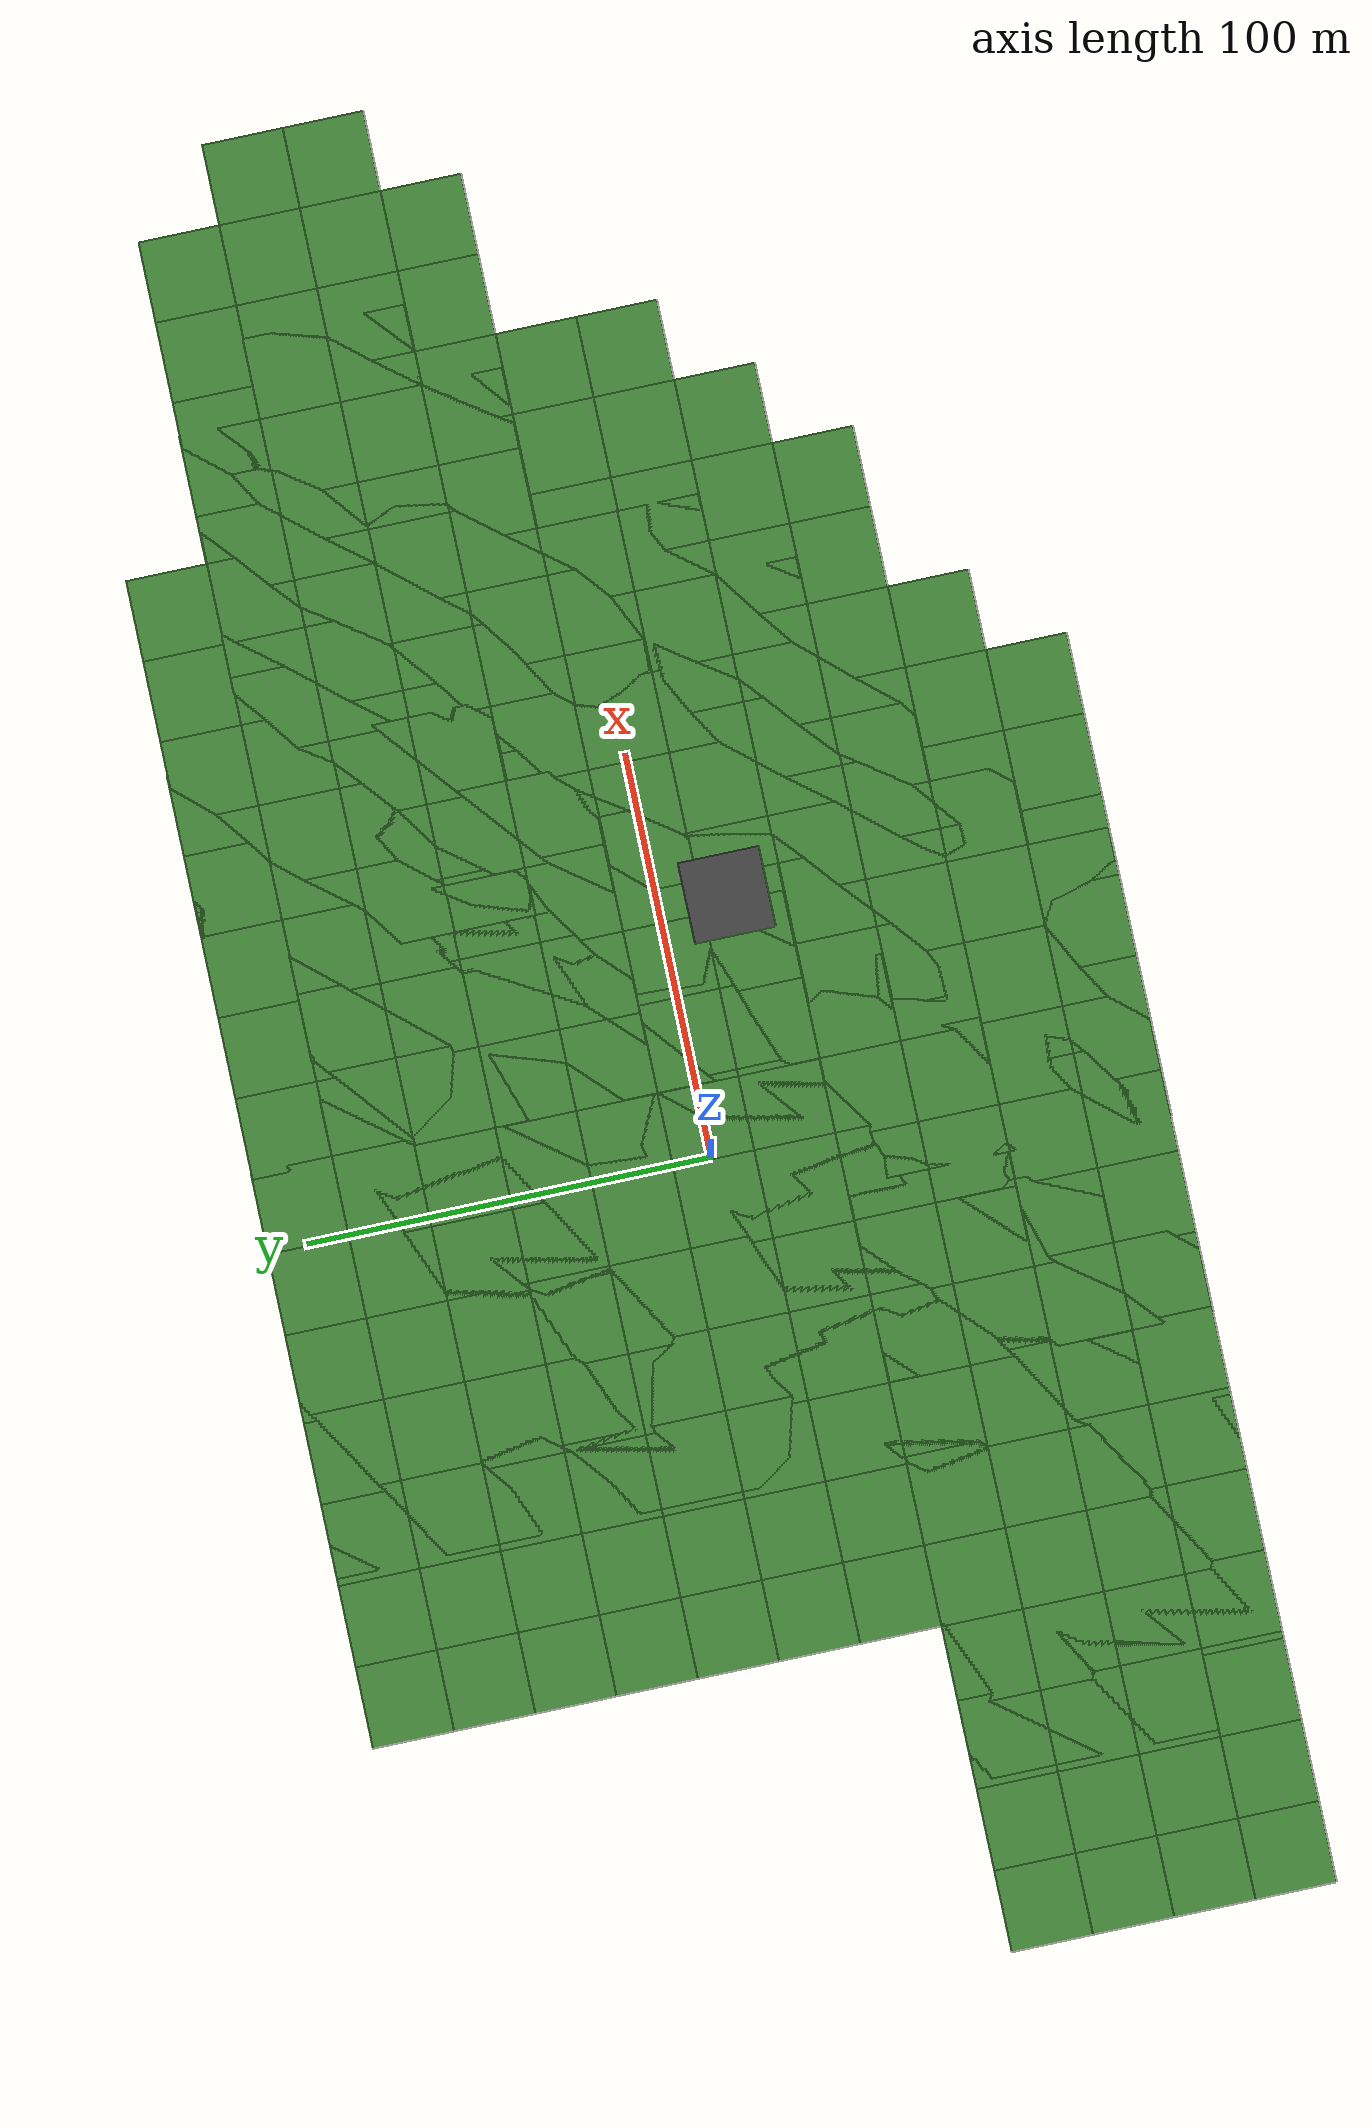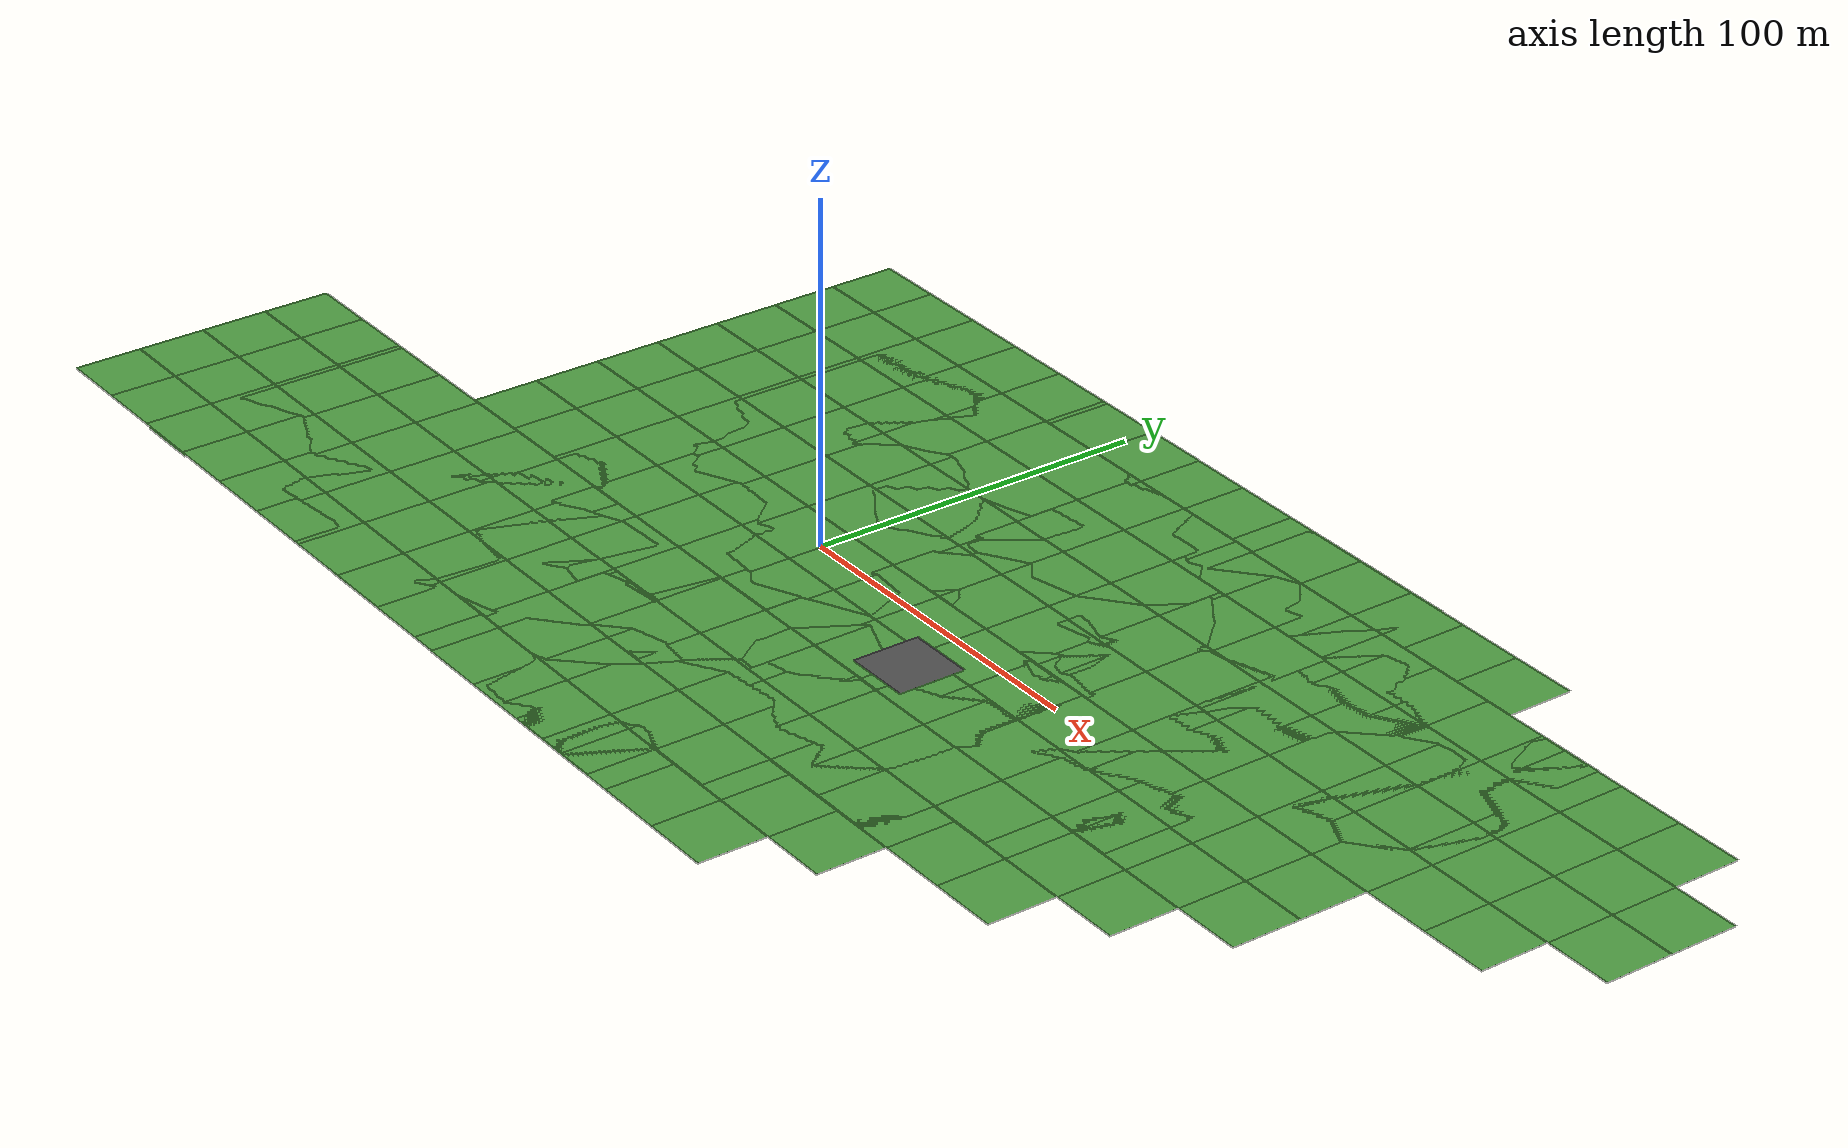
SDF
<sdf version="1.7">
 <world name="default">
  <scene>
   <grid>0</grid>
   <origin_visual>0</origin_visual>
   <ambient>0.85 0.85 0.85 1</ambient>
   <sky><clouds><speed>12</speed></clouds></sky>
   <background>0.35 0.35 0.35 1</background>
   <shadows>1</shadows>
  </scene>
  <physics name="default_physics" default="0" type="ode">
   <max_step_size>0.005</max_step_size>
   <real_time_factor>1</real_time_factor>
   <real_time_update_rate>200</real_time_update_rate>
  </physics>
  <light name="sun" type="directional">
   <pose>0 0 1000 0 -0 0</pose>
   <diffuse>0.8 0.8 0.8 1</diffuse>
   <specular>0.5 0.5 0.5 1</specular>
   <attenuation>
    <range>1000</range>
    <constant>0.9</constant>
    <linear>0.01</linear>
    <quadratic>0.001</quadratic>
   </attenuation>
   <direction>-0.5 0.1 -0.4</direction>
   <spot><inner_angle>0</inner_angle><outer_angle>0</outer_angle><falloff>0</falloff></spot>
  </light>
  <model name="ground_plane">
   <static>1</static>
   <link name="link">
    <collision name="collision">
     <geometry><plane><normal>0 0 1</normal><size>100 100</size></plane></geometry>
     <surface><friction><ode><mu>100</mu><mu2>50</mu2></ode></friction></surface>
    </collision>
   </link>
  </model>
  <model name="asphalt_plane_74">
   <static>1</static>
   <pose>61.581 -16.664 0 0 -0 0</pose>
   <link name="link">
    <visual name="visual">
     <geometry><box><size>20 20 0.05</size></box></geometry>
     <material>
      <script>
       <uri>model://asphalt_plane/materials/scripts</uri>
       <uri>model://asphalt_plane/materials/textures</uri>
       <name>vrc/asphalt</name>
      </script>
     </material>
    </visual>
   </link>
  </model>
  <gravity>0 0 -9.8</gravity>
  <magnetic_field>6e-06 2.3e-05 -4.2e-05</magnetic_field>
  <atmosphere type="adiabatic"/>
  <audio><device>default</device></audio>
  <spherical_coordinates>
   <surface_model>EARTH_WGS84</surface_model>
   <latitude_deg>0</latitude_deg>
   <longitude_deg>0</longitude_deg>
   <elevation>0</elevation>
   <heading_deg>0</heading_deg>
  </spherical_coordinates>
  <model name="grass_plane">
   <static>1</static>
   <link name="link">
    <collision name="collision">
     <geometry><plane><normal>0 0 1</normal><size>500 500</size></plane></geometry>
     <surface><friction><ode><mu>0.5</mu><mu2>0.5</mu2></ode></friction></surface>
    </collision>
    <visual name="visual_0">
     <pose>-40 -40 0 0 -0 0</pose>
     <cast_shadows>0</cast_shadows>
     <geometry><plane><normal>0 0 1</normal><size>20 20</size></plane></geometry>
     <material>
      <script>
       <uri>model://grass_plane/materials/scripts</uri>
       <uri>model://grass_plane/materials/textures</uri>
       <name>vrc/grass</name>
      </script>
     </material>
    </visual>
    <visual name="visual_1">
     <pose>-20 -40 0 0 -0 0</pose>
     <cast_shadows>0</cast_shadows>
     <geometry><plane><normal>0 0 1</normal><size>20 20</size></plane></geometry>
     <material>
      <script>
       <uri>model://grass_plane/materials/scripts</uri>
       <uri>model://grass_plane/materials/textures</uri>
       <name>vrc/grass</name>
      </script>
     </material>
    </visual>
    <visual name="visual_2">
     <pose>0 -40 0 0 -0 0</pose>
     <cast_shadows>0</cast_shadows>
     <geometry><plane><normal>0 0 1</normal><size>20 20</size></plane></geometry>
     <material>
      <script>
       <uri>model://grass_plane/materials/scripts</uri>
       <uri>model://grass_plane/materials/textures</uri>
       <name>vrc/grass</name>
      </script>
     </material>
    </visual>
    <visual name="visual_3">
     <pose>20 -40 0 0 -0 0</pose>
     <cast_shadows>0</cast_shadows>
     <geometry><plane><normal>0 0 1</normal><size>20 20</size></plane></geometry>
     <material>
      <script>
       <uri>model://grass_plane/materials/scripts</uri>
       <uri>model://grass_plane/materials/textures</uri>
       <name>vrc/grass</name>
      </script>
     </material>
    </visual>
    <visual name="visual_4">
     <pose>40 -40 0 0 -0 0</pose>
     <cast_shadows>0</cast_shadows>
     <geometry><plane><normal>0 0 1</normal><size>20 20</size></plane></geometry>
     <material>
      <script>
       <uri>model://grass_plane/materials/scripts</uri>
       <uri>model://grass_plane/materials/textures</uri>
       <name>vrc/grass</name>
      </script>
     </material>
    </visual>
    <visual name="visual_5">
     <pose>60 -40 0 0 -0 0</pose>
     <cast_shadows>0</cast_shadows>
     <geometry><plane><normal>0 0 1</normal><size>20 20</size></plane></geometry>
     <material>
      <script>
       <uri>model://grass_plane/materials/scripts</uri>
       <uri>model://grass_plane/materials/textures</uri>
       <name>vrc/grass</name>
      </script>
     </material>
    </visual>
    <visual name="visual_6">
     <pose>-40 -20 0 0 -0 0</pose>
     <cast_shadows>0</cast_shadows>
     <geometry><plane><normal>0 0 1</normal><size>20 20</size></plane></geometry>
     <material>
      <script>
       <uri>model://grass_plane/materials/scripts</uri>
       <uri>model://grass_plane/materials/textures</uri>
       <name>vrc/grass</name>
      </script>
     </material>
    </visual>
    <visual name="visual_7">
     <pose>-20 -20 0 0 -0 0</pose>
     <cast_shadows>0</cast_shadows>
     <geometry><plane><normal>0 0 1</normal><size>20 20</size></plane></geometry>
     <material>
      <script>
       <uri>model://grass_plane/materials/scripts</uri>
       <uri>model://grass_plane/materials/textures</uri>
       <name>vrc/grass</name>
      </script>
     </material>
    </visual>
    <visual name="visual_8">
     <pose>0 -20 0 0 -0 0</pose>
     <cast_shadows>0</cast_shadows>
     <geometry><plane><normal>0 0 1</normal><size>20 20</size></plane></geometry>
     <material>
      <script>
       <uri>model://grass_plane/materials/scripts</uri>
       <uri>model://grass_plane/materials/textures</uri>
       <name>vrc/grass</name>
      </script>
     </material>
    </visual>
    <visual name="visual_9">
     <pose>20 -20 0 0 -0 0</pose>
     <cast_shadows>0</cast_shadows>
     <geometry><plane><normal>0 0 1</normal><size>20 20</size></plane></geometry>
     <material>
      <script>
       <uri>model://grass_plane/materials/scripts</uri>
       <uri>model://grass_plane/materials/textures</uri>
       <name>vrc/grass</name>
      </script>
     </material>
    </visual>
    <visual name="visual_10">
     <pose>40 -20 0 0 -0 0</pose>
     <cast_shadows>0</cast_shadows>
     <geometry><plane><normal>0 0 1</normal><size>20 20</size></plane></geometry>
     <material>
      <script>
       <uri>model://grass_plane/materials/scripts</uri>
       <uri>model://grass_plane/materials/textures</uri>
       <name>vrc/grass</name>
      </script>
     </material>
    </visual>
    <visual name="visual_11">
     <pose>60 -20 0 0 -0 0</pose>
     <cast_shadows>0</cast_shadows>
     <geometry><plane><normal>0 0 1</normal><size>20 20</size></plane></geometry>
     <material>
      <script>
       <uri>model://grass_plane/materials/scripts</uri>
       <uri>model://grass_plane/materials/textures</uri>
       <name>vrc/grass</name>
      </script>
     </material>
    </visual>
    <visual name="visual_12">
     <pose>80 -20 0 0 -0 0</pose>
     <cast_shadows>0</cast_shadows>
     <geometry><plane><normal>0 0 1</normal><size>20 20</size></plane></geometry>
     <material>
      <script>
       <uri>model://grass_plane/materials/scripts</uri>
       <uri>model://grass_plane/materials/textures</uri>
       <name>vrc/grass</name>
      </script>
     </material>
    </visual>
    <visual name="visual_13">
     <pose>-40 0 0 0 -0 0</pose>
     <cast_shadows>0</cast_shadows>
     <geometry><plane><normal>0 0 1</normal><size>20 20</size></plane></geometry>
     <material>
      <script>
       <uri>model://grass_plane/materials/scripts</uri>
       <uri>model://grass_plane/materials/textures</uri>
       <name>vrc/grass</name>
      </script>
     </material>
    </visual>
    <visual name="visual_14">
     <pose>-20 0 0 0 -0 0</pose>
     <cast_shadows>0</cast_shadows>
     <geometry><plane><normal>0 0 1</normal><size>20 20</size></plane></geometry>
     <material>
      <script>
       <uri>model://grass_plane/materials/scripts</uri>
       <uri>model://grass_plane/materials/textures</uri>
       <name>vrc/grass</name>
      </script>
     </material>
    </visual>
    <visual name="visual_15">
     <cast_shadows>0</cast_shadows>
     <geometry><plane><normal>0 0 1</normal><size>20 20</size></plane></geometry>
     <material>
      <script>
       <uri>model://grass_plane/materials/scripts</uri>
       <uri>model://grass_plane/materials/textures</uri>
       <name>vrc/grass</name>
      </script>
     </material>
    </visual>
    <visual name="visual_16">
     <pose>20 0 0 0 -0 0</pose>
     <cast_shadows>0</cast_shadows>
     <geometry><plane><normal>0 0 1</normal><size>20 20</size></plane></geometry>
     <material>
      <script>
       <uri>model://grass_plane/materials/scripts</uri>
       <uri>model://grass_plane/materials/textures</uri>
       <name>vrc/grass</name>
      </script>
     </material>
    </visual>
    <visual name="visual_17">
     <pose>40 0 0 0 -0 0</pose>
     <cast_shadows>0</cast_shadows>
     <geometry><plane><normal>0 0 1</normal><size>20 20</size></plane></geometry>
     <material>
      <script>
       <uri>model://grass_plane/materials/scripts</uri>
       <uri>model://grass_plane/materials/textures</uri>
       <name>vrc/grass</name>
      </script>
     </material>
    </visual>
    <visual name="visual_18">
     <pose>60 0 0 0 -0 0</pose>
     <cast_shadows>0</cast_shadows>
     <geometry><plane><normal>0 0 1</normal><size>20 20</size></plane></geometry>
     <material>
      <script>
       <uri>model://grass_plane/materials/scripts</uri>
       <uri>model://grass_plane/materials/textures</uri>
       <name>vrc/grass</name>
      </script>
     </material>
    </visual>
    <visual name="visual_19">
     <pose>80 0 0 0 -0 0</pose>
     <cast_shadows>0</cast_shadows>
     <geometry><plane><normal>0 0 1</normal><size>20 20</size></plane></geometry>
     <material>
      <script>
       <uri>model://grass_plane/materials/scripts</uri>
       <uri>model://grass_plane/materials/textures</uri>
       <name>vrc/grass</name>
      </script>
     </material>
    </visual>
    <visual name="visual_20">
     <pose>100 0 0 0 -0 0</pose>
     <cast_shadows>0</cast_shadows>
     <geometry><plane><normal>0 0 1</normal><size>20 20</size></plane></geometry>
     <material>
      <script>
       <uri>model://grass_plane/materials/scripts</uri>
       <uri>model://grass_plane/materials/textures</uri>
       <name>vrc/grass</name>
      </script>
     </material>
    </visual>
    <visual name="visual_21">
     <pose>120 0 0 0 -0 0</pose>
     <cast_shadows>0</cast_shadows>
     <geometry><plane><normal>0 0 1</normal><size>20 20</size></plane></geometry>
     <material>
      <script>
       <uri>model://grass_plane/materials/scripts</uri>
       <uri>model://grass_plane/materials/textures</uri>
       <name>vrc/grass</name>
      </script>
     </material>
    </visual>
    <visual name="visual_22">
     <pose>-40 20 0 0 -0 0</pose>
     <cast_shadows>0</cast_shadows>
     <geometry><plane><normal>0 0 1</normal><size>20 20</size></plane></geometry>
     <material>
      <script>
       <uri>model://grass_plane/materials/scripts</uri>
       <uri>model://grass_plane/materials/textures</uri>
       <name>vrc/grass</name>
      </script>
     </material>
    </visual>
    <visual name="visual_23">
     <pose>-20 20 0 0 -0 0</pose>
     <cast_shadows>0</cast_shadows>
     <geometry><plane><normal>0 0 1</normal><size>20 20</size></plane></geometry>
     <material>
      <script>
       <uri>model://grass_plane/materials/scripts</uri>
       <uri>model://grass_plane/materials/textures</uri>
       <name>vrc/grass</name>
      </script>
     </material>
    </visual>
    <visual name="visual_24">
     <pose>0 20 0 0 -0 0</pose>
     <cast_shadows>0</cast_shadows>
     <geometry><plane><normal>0 0 1</normal><size>20 20</size></plane></geometry>
     <material>
      <script>
       <uri>model://grass_plane/materials/scripts</uri>
       <uri>model://grass_plane/materials/textures</uri>
       <name>vrc/grass</name>
      </script>
     </material>
    </visual>
    <visual name="visual_25">
     <pose>20 20 0 0 -0 0</pose>
     <cast_shadows>0</cast_shadows>
     <geometry><plane><normal>0 0 1</normal><size>20 20</size></plane></geometry>
     <material>
      <script>
       <uri>model://grass_plane/materials/scripts</uri>
       <uri>model://grass_plane/materials/textures</uri>
       <name>vrc/grass</name>
      </script>
     </material>
    </visual>
    <visual name="visual_26">
     <pose>40 20 0 0 -0 0</pose>
     <cast_shadows>0</cast_shadows>
     <geometry><plane><normal>0 0 1</normal><size>20 20</size></plane></geometry>
     <material>
      <script>
       <uri>model://grass_plane/materials/scripts</uri>
       <uri>model://grass_plane/materials/textures</uri>
       <name>vrc/grass</name>
      </script>
     </material>
    </visual>
    <visual name="visual_27">
     <pose>60 20 0 0 -0 0</pose>
     <cast_shadows>0</cast_shadows>
     <geometry><plane><normal>0 0 1</normal><size>20 20</size></plane></geometry>
     <material>
      <script>
       <uri>model://grass_plane/materials/scripts</uri>
       <uri>model://grass_plane/materials/textures</uri>
       <name>vrc/grass</name>
      </script>
     </material>
    </visual>
    <visual name="visual_28">
     <pose>80 20 0 0 -0 0</pose>
     <cast_shadows>0</cast_shadows>
     <geometry><plane><normal>0 0 1</normal><size>20 20</size></plane></geometry>
     <material>
      <script>
       <uri>model://grass_plane/materials/scripts</uri>
       <uri>model://grass_plane/materials/textures</uri>
       <name>vrc/grass</name>
      </script>
     </material>
    </visual>
    <visual name="visual_29">
     <pose>100 20 0 0 -0 0</pose>
     <cast_shadows>0</cast_shadows>
     <geometry><plane><normal>0 0 1</normal><size>20 20</size></plane></geometry>
     <material>
      <script>
       <uri>model://grass_plane/materials/scripts</uri>
       <uri>model://grass_plane/materials/textures</uri>
       <name>vrc/grass</name>
      </script>
     </material>
    </visual>
    <visual name="visual_30">
     <pose>120 20 0 0 -0 0</pose>
     <cast_shadows>0</cast_shadows>
     <geometry><plane><normal>0 0 1</normal><size>20 20</size></plane></geometry>
     <material>
      <script>
       <uri>model://grass_plane/materials/scripts</uri>
       <uri>model://grass_plane/materials/textures</uri>
       <name>vrc/grass</name>
      </script>
     </material>
    </visual>
    <visual name="visual_31">
     <pose>140 20 0 0 -0 0</pose>
     <cast_shadows>0</cast_shadows>
     <geometry><plane><normal>0 0 1</normal><size>20 20</size></plane></geometry>
     <material>
      <script>
       <uri>model://grass_plane/materials/scripts</uri>
       <uri>model://grass_plane/materials/textures</uri>
       <name>vrc/grass</name>
      </script>
     </material>
    </visual>
    <visual name="visual_32">
     <pose>40 40 0 0 -0 0</pose>
     <cast_shadows>0</cast_shadows>
     <geometry><plane><normal>0 0 1</normal><size>20 20</size></plane></geometry>
     <material>
      <script>
       <uri>model://grass_plane/materials/scripts</uri>
       <uri>model://grass_plane/materials/textures</uri>
       <name>vrc/grass</name>
      </script>
     </material>
    </visual>
    <visual name="visual_33">
     <pose>60 40 0 0 -0 0</pose>
     <cast_shadows>0</cast_shadows>
     <geometry><plane><normal>0 0 1</normal><size>20 20</size></plane></geometry>
     <material>
      <script>
       <uri>model://grass_plane/materials/scripts</uri>
       <uri>model://grass_plane/materials/textures</uri>
       <name>vrc/grass</name>
      </script>
     </material>
    </visual>
    <visual name="visual_34">
     <pose>80 40 0 0 -0 0</pose>
     <cast_shadows>0</cast_shadows>
     <geometry><plane><normal>0 0 1</normal><size>20 20</size></plane></geometry>
     <material>
      <script>
       <uri>model://grass_plane/materials/scripts</uri>
       <uri>model://grass_plane/materials/textures</uri>
       <name>vrc/grass</name>
      </script>
     </material>
    </visual>
    <visual name="visual_35">
     <pose>100 40 0 0 -0 0</pose>
     <cast_shadows>0</cast_shadows>
     <geometry><plane><normal>0 0 1</normal><size>20 20</size></plane></geometry>
     <material>
      <script>
       <uri>model://grass_plane/materials/scripts</uri>
       <uri>model://grass_plane/materials/textures</uri>
       <name>vrc/grass</name>
      </script>
     </material>
    </visual>
    <visual name="visual_36">
     <pose>120 40 0 0 -0 0</pose>
     <cast_shadows>0</cast_shadows>
     <geometry><plane><normal>0 0 1</normal><size>20 20</size></plane></geometry>
     <material>
      <script>
       <uri>model://grass_plane/materials/scripts</uri>
       <uri>model://grass_plane/materials/textures</uri>
       <name>vrc/grass</name>
      </script>
     </material>
    </visual>
    <visual name="visual_37">
     <pose>140 40 0 0 -0 0</pose>
     <cast_shadows>0</cast_shadows>
     <geometry><plane><normal>0 0 1</normal><size>20 20</size></plane></geometry>
     <material>
      <script>
       <uri>model://grass_plane/materials/scripts</uri>
       <uri>model://grass_plane/materials/textures</uri>
       <name>vrc/grass</name>
      </script>
     </material>
    </visual>
    <visual name="visual_38">
     <pose>160 40 0 0 -0 0</pose>
     <cast_shadows>0</cast_shadows>
     <geometry><plane><normal>0 0 1</normal><size>20 20</size></plane></geometry>
     <material>
      <script>
       <uri>model://grass_plane/materials/scripts</uri>
       <uri>model://grass_plane/materials/textures</uri>
       <name>vrc/grass</name>
      </script>
     </material>
    </visual>
    <visual name="visual_39">
     <pose>40 60 0 0 -0 0</pose>
     <cast_shadows>0</cast_shadows>
     <geometry><plane><normal>0 0 1</normal><size>20 20</size></plane></geometry>
     <material>
      <script>
       <uri>model://grass_plane/materials/scripts</uri>
       <uri>model://grass_plane/materials/textures</uri>
       <name>vrc/grass</name>
      </script>
     </material>
    </visual>
    <visual name="visual_40">
     <pose>60 60 0 0 -0 0</pose>
     <cast_shadows>0</cast_shadows>
     <geometry><plane><normal>0 0 1</normal><size>20 20</size></plane></geometry>
     <material>
      <script>
       <uri>model://grass_plane/materials/scripts</uri>
       <uri>model://grass_plane/materials/textures</uri>
       <name>vrc/grass</name>
      </script>
     </material>
    </visual>
    <visual name="visual_41">
     <pose>80 60 0 0 -0 0</pose>
     <cast_shadows>0</cast_shadows>
     <geometry><plane><normal>0 0 1</normal><size>20 20</size></plane></geometry>
     <material>
      <script>
       <uri>model://grass_plane/materials/scripts</uri>
       <uri>model://grass_plane/materials/textures</uri>
       <name>vrc/grass</name>
      </script>
     </material>
    </visual>
    <visual name="visual_42">
     <pose>100 60 0 0 -0 0</pose>
     <cast_shadows>0</cast_shadows>
     <geometry><plane><normal>0 0 1</normal><size>20 20</size></plane></geometry>
     <material>
      <script>
       <uri>model://grass_plane/materials/scripts</uri>
       <uri>model://grass_plane/materials/textures</uri>
       <name>vrc/grass</name>
      </script>
     </material>
    </visual>
    <visual name="visual_43">
     <pose>120 60 0 0 -0 0</pose>
     <cast_shadows>0</cast_shadows>
     <geometry><plane><normal>0 0 1</normal><size>20 20</size></plane></geometry>
     <material>
      <script>
       <uri>model://grass_plane/materials/scripts</uri>
       <uri>model://grass_plane/materials/textures</uri>
       <name>vrc/grass</name>
      </script>
     </material>
    </visual>
    <visual name="visual_44">
     <pose>140 60 0 0 -0 0</pose>
     <cast_shadows>0</cast_shadows>
     <geometry><plane><normal>0 0 1</normal><size>20 20</size></plane></geometry>
     <material>
      <script>
       <uri>model://grass_plane/materials/scripts</uri>
       <uri>model://grass_plane/materials/textures</uri>
       <name>vrc/grass</name>
      </script>
     </material>
    </visual>
    <visual name="visual_45">
     <pose>160 60 0 0 -0 0</pose>
     <cast_shadows>0</cast_shadows>
     <geometry><plane><normal>0 0 1</normal><size>20 20</size></plane></geometry>
     <material>
      <script>
       <uri>model://grass_plane/materials/scripts</uri>
       <uri>model://grass_plane/materials/textures</uri>
       <name>vrc/grass</name>
      </script>
     </material>
    </visual>
    <visual name="visual_46">
     <pose>40 80 0 0 -0 0</pose>
     <cast_shadows>0</cast_shadows>
     <geometry><plane><normal>0 0 1</normal><size>20 20</size></plane></geometry>
     <material>
      <script>
       <uri>model://grass_plane/materials/scripts</uri>
       <uri>model://grass_plane/materials/textures</uri>
       <name>vrc/grass</name>
      </script>
     </material>
    </visual>
    <visual name="visual_47">
     <pose>60 80 0 0 -0 0</pose>
     <cast_shadows>0</cast_shadows>
     <geometry><plane><normal>0 0 1</normal><size>20 20</size></plane></geometry>
     <material>
      <script>
       <uri>model://grass_plane/materials/scripts</uri>
       <uri>model://grass_plane/materials/textures</uri>
       <name>vrc/grass</name>
      </script>
     </material>
    </visual>
    <visual name="visual_48">
     <pose>80 80 0 0 -0 0</pose>
     <cast_shadows>0</cast_shadows>
     <geometry><plane><normal>0 0 1</normal><size>20 20</size></plane></geometry>
     <material>
      <script>
       <uri>model://grass_plane/materials/scripts</uri>
       <uri>model://grass_plane/materials/textures</uri>
       <name>vrc/grass</name>
      </script>
     </material>
    </visual>
    <visual name="visual_49">
     <pose>100 80 0 0 -0 0</pose>
     <cast_shadows>0</cast_shadows>
     <geometry><plane><normal>0 0 1</normal><size>20 20</size></plane></geometry>
     <material>
      <script>
       <uri>model://grass_plane/materials/scripts</uri>
       <uri>model://grass_plane/materials/textures</uri>
       <name>vrc/grass</name>
      </script>
     </material>
    </visual>
    <visual name="visual_50">
     <pose>120 80 0 0 -0 0</pose>
     <cast_shadows>0</cast_shadows>
     <geometry><plane><normal>0 0 1</normal><size>20 20</size></plane></geometry>
     <material>
      <script>
       <uri>model://grass_plane/materials/scripts</uri>
       <uri>model://grass_plane/materials/textures</uri>
       <name>vrc/grass</name>
      </script>
     </material>
    </visual>
    <visual name="visual_51">
     <pose>140 80 0 0 -0 0</pose>
     <cast_shadows>0</cast_shadows>
     <geometry><plane><normal>0 0 1</normal><size>20 20</size></plane></geometry>
     <material>
      <script>
       <uri>model://grass_plane/materials/scripts</uri>
       <uri>model://grass_plane/materials/textures</uri>
       <name>vrc/grass</name>
      </script>
     </material>
    </visual>
    <visual name="visual_52">
     <pose>160 80 0 0 -0 0</pose>
     <cast_shadows>0</cast_shadows>
     <geometry><plane><normal>0 0 1</normal><size>20 20</size></plane></geometry>
     <material>
      <script>
       <uri>model://grass_plane/materials/scripts</uri>
       <uri>model://grass_plane/materials/textures</uri>
       <name>vrc/grass</name>
      </script>
     </material>
    </visual>
    <visual name="visual_53">
     <pose>180 80 0 0 -0 0</pose>
     <cast_shadows>0</cast_shadows>
     <geometry><plane><normal>0 0 1</normal><size>20 20</size></plane></geometry>
     <material>
      <script>
       <uri>model://grass_plane/materials/scripts</uri>
       <uri>model://grass_plane/materials/textures</uri>
       <name>vrc/grass</name>
      </script>
     </material>
    </visual>
    <visual name="visual_54">
     <pose>200 80 0 0 -0 0</pose>
     <cast_shadows>0</cast_shadows>
     <geometry><plane><normal>0 0 1</normal><size>20 20</size></plane></geometry>
     <material>
      <script>
       <uri>model://grass_plane/materials/scripts</uri>
       <uri>model://grass_plane/materials/textures</uri>
       <name>vrc/grass</name>
      </script>
     </material>
    </visual>
    <visual name="visual_55">
     <pose>40 100 0 0 -0 0</pose>
     <cast_shadows>0</cast_shadows>
     <geometry><plane><normal>0 0 1</normal><size>20 20</size></plane></geometry>
     <material>
      <script>
       <uri>model://grass_plane/materials/scripts</uri>
       <uri>model://grass_plane/materials/textures</uri>
       <name>vrc/grass</name>
      </script>
     </material>
    </visual>
    <visual name="visual_56">
     <pose>60 100 0 0 -0 0</pose>
     <cast_shadows>0</cast_shadows>
     <geometry><plane><normal>0 0 1</normal><size>20 20</size></plane></geometry>
     <material>
      <script>
       <uri>model://grass_plane/materials/scripts</uri>
       <uri>model://grass_plane/materials/textures</uri>
       <name>vrc/grass</name>
      </script>
     </material>
    </visual>
    <visual name="visual_57">
     <pose>80 100 0 0 -0 0</pose>
     <cast_shadows>0</cast_shadows>
     <geometry><plane><normal>0 0 1</normal><size>20 20</size></plane></geometry>
     <material>
      <script>
       <uri>model://grass_plane/materials/scripts</uri>
       <uri>model://grass_plane/materials/textures</uri>
       <name>vrc/grass</name>
      </script>
     </material>
    </visual>
    <visual name="visual_58">
     <pose>100 100 0 0 -0 0</pose>
     <cast_shadows>0</cast_shadows>
     <geometry><plane><normal>0 0 1</normal><size>20 20</size></plane></geometry>
     <material>
      <script>
       <uri>model://grass_plane/materials/scripts</uri>
       <uri>model://grass_plane/materials/textures</uri>
       <name>vrc/grass</name>
      </script>
     </material>
    </visual>
    <visual name="visual_59">
     <pose>120 100 0 0 -0 0</pose>
     <cast_shadows>0</cast_shadows>
     <geometry><plane><normal>0 0 1</normal><size>20 20</size></plane></geometry>
     <material>
      <script>
       <uri>model://grass_plane/materials/scripts</uri>
       <uri>model://grass_plane/materials/textures</uri>
       <name>vrc/grass</name>
      </script>
     </material>
    </visual>
    <visual name="visual_60">
     <pose>140 100 0 0 -0 0</pose>
     <cast_shadows>0</cast_shadows>
     <geometry><plane><normal>0 0 1</normal><size>20 20</size></plane></geometry>
     <material>
      <script>
       <uri>model://grass_plane/materials/scripts</uri>
       <uri>model://grass_plane/materials/textures</uri>
       <name>vrc/grass</name>
      </script>
     </material>
    </visual>
    <visual name="visual_61">
     <pose>160 100 0 0 -0 0</pose>
     <cast_shadows>0</cast_shadows>
     <geometry><plane><normal>0 0 1</normal><size>20 20</size></plane></geometry>
     <material>
      <script>
       <uri>model://grass_plane/materials/scripts</uri>
       <uri>model://grass_plane/materials/textures</uri>
       <name>vrc/grass</name>
      </script>
     </material>
    </visual>
    <visual name="visual_62">
     <pose>180 100 0 0 -0 0</pose>
     <cast_shadows>0</cast_shadows>
     <geometry><plane><normal>0 0 1</normal><size>20 20</size></plane></geometry>
     <material>
      <script>
       <uri>model://grass_plane/materials/scripts</uri>
       <uri>model://grass_plane/materials/textures</uri>
       <name>vrc/grass</name>
      </script>
     </material>
    </visual>
    <visual name="visual_63">
     <pose>200 100 0 0 -0 0</pose>
     <cast_shadows>0</cast_shadows>
     <geometry><plane><normal>0 0 1</normal><size>20 20</size></plane></geometry>
     <material>
      <script>
       <uri>model://grass_plane/materials/scripts</uri>
       <uri>model://grass_plane/materials/textures</uri>
       <name>vrc/grass</name>
      </script>
     </material>
    </visual>
    <visual name="visual_63a">
     <pose>220 100 0 0 -0 0</pose>
     <cast_shadows>0</cast_shadows>
     <geometry><plane><normal>0 0 1</normal><size>20 20</size></plane></geometry>
     <material>
      <script>
       <uri>model://grass_plane/materials/scripts</uri>
       <uri>model://grass_plane/materials/textures</uri>
       <name>vrc/grass</name>
      </script>
     </material>
    </visual>
    <visual name="visual_64">
     <pose>40 120 0 0 -0 0</pose>
     <cast_shadows>0</cast_shadows>
     <geometry><plane><normal>0 0 1</normal><size>20 20</size></plane></geometry>
     <material>
      <script>
       <uri>model://grass_plane/materials/scripts</uri>
       <uri>model://grass_plane/materials/textures</uri>
       <name>vrc/grass</name>
      </script>
     </material>
    </visual>
    <visual name="visual_65">
     <pose>60 120 0 0 -0 0</pose>
     <cast_shadows>0</cast_shadows>
     <geometry><plane><normal>0 0 1</normal><size>20 20</size></plane></geometry>
     <material>
      <script>
       <uri>model://grass_plane/materials/scripts</uri>
       <uri>model://grass_plane/materials/textures</uri>
       <name>vrc/grass</name>
      </script>
     </material>
    </visual>
    <visual name="visual_66">
     <pose>80 120 0 0 -0 0</pose>
     <cast_shadows>0</cast_shadows>
     <geometry><plane><normal>0 0 1</normal><size>20 20</size></plane></geometry>
     <material>
      <script>
       <uri>model://grass_plane/materials/scripts</uri>
       <uri>model://grass_plane/materials/textures</uri>
       <name>vrc/grass</name>
      </script>
     </material>
    </visual>
    <visual name="visual_67">
     <pose>100 120 0 0 -0 0</pose>
     <cast_shadows>0</cast_shadows>
     <geometry><plane><normal>0 0 1</normal><size>20 20</size></plane></geometry>
     <material>
      <script>
       <uri>model://grass_plane/materials/scripts</uri>
       <uri>model://grass_plane/materials/textures</uri>
       <name>vrc/grass</name>
      </script>
     </material>
    </visual>
    <visual name="visual_68">
     <pose>120 120 0 0 -0 0</pose>
     <cast_shadows>0</cast_shadows>
     <geometry><plane><normal>0 0 1</normal><size>20 20</size></plane></geometry>
     <material>
      <script>
       <uri>model://grass_plane/materials/scripts</uri>
       <uri>model://grass_plane/materials/textures</uri>
       <name>vrc/grass</name>
      </script>
     </material>
    </visual>
    <visual name="visual_69">
     <pose>140 120 0 0 -0 0</pose>
     <cast_shadows>0</cast_shadows>
     <geometry><plane><normal>0 0 1</normal><size>20 20</size></plane></geometry>
     <material>
      <script>
       <uri>model://grass_plane/materials/scripts</uri>
       <uri>model://grass_plane/materials/textures</uri>
       <name>vrc/grass</name>
      </script>
     </material>
    </visual>
    <visual name="visual_70">
     <pose>160 120 0 0 -0 0</pose>
     <cast_shadows>0</cast_shadows>
     <geometry><plane><normal>0 0 1</normal><size>20 20</size></plane></geometry>
     <material>
      <script>
       <uri>model://grass_plane/materials/scripts</uri>
       <uri>model://grass_plane/materials/textures</uri>
       <name>vrc/grass</name>
      </script>
     </material>
    </visual>
    <visual name="visual_71">
     <pose>180 120 0 0 -0 0</pose>
     <cast_shadows>0</cast_shadows>
     <geometry><plane><normal>0 0 1</normal><size>20 20</size></plane></geometry>
     <material>
      <script>
       <uri>model://grass_plane/materials/scripts</uri>
       <uri>model://grass_plane/materials/textures</uri>
       <name>vrc/grass</name>
      </script>
     </material>
    </visual>
    <visual name="visual_72">
     <pose>200 120 0 0 -0 0</pose>
     <cast_shadows>0</cast_shadows>
     <geometry><plane><normal>0 0 1</normal><size>20 20</size></plane></geometry>
     <material>
      <script>
       <uri>model://grass_plane/materials/scripts</uri>
       <uri>model://grass_plane/materials/textures</uri>
       <name>vrc/grass</name>
      </script>
     </material>
    </visual>
    <visual name="visual_72a">
     <pose>220 120 0 0 -0 0</pose>
     <cast_shadows>0</cast_shadows>
     <geometry><plane><normal>0 0 1</normal><size>20 20</size></plane></geometry>
     <material>
      <script>
       <uri>model://grass_plane/materials/scripts</uri>
       <uri>model://grass_plane/materials/textures</uri>
       <name>vrc/grass</name>
      </script>
     </material>
    </visual>
    <visual name="visual_73">
     <pose>40 140 0 0 -0 0</pose>
     <cast_shadows>0</cast_shadows>
     <geometry><plane><normal>0 0 1</normal><size>20 20</size></plane></geometry>
     <material>
      <script>
       <uri>model://grass_plane/materials/scripts</uri>
       <uri>model://grass_plane/materials/textures</uri>
       <name>vrc/grass</name>
      </script>
     </material>
    </visual>
    <visual name="visual_74">
     <pose>60 140 0 0 -0 0</pose>
     <cast_shadows>0</cast_shadows>
     <geometry><plane><normal>0 0 1</normal><size>20 20</size></plane></geometry>
     <material>
      <script>
       <uri>model://grass_plane/materials/scripts</uri>
       <uri>model://grass_plane/materials/textures</uri>
       <name>vrc/grass</name>
      </script>
     </material>
    </visual>
    <visual name="visual_75">
     <pose>80 140 0 0 -0 0</pose>
     <cast_shadows>0</cast_shadows>
     <geometry><plane><normal>0 0 1</normal><size>20 20</size></plane></geometry>
     <material>
      <script>
       <uri>model://grass_plane/materials/scripts</uri>
       <uri>model://grass_plane/materials/textures</uri>
       <name>vrc/grass</name>
      </script>
     </material>
    </visual>
    <visual name="visual_76">
     <pose>100 140 0 0 -0 0</pose>
     <cast_shadows>0</cast_shadows>
     <geometry><plane><normal>0 0 1</normal><size>20 20</size></plane></geometry>
     <material>
      <script>
       <uri>model://grass_plane/materials/scripts</uri>
       <uri>model://grass_plane/materials/textures</uri>
       <name>vrc/grass</name>
      </script>
     </material>
    </visual>
    <visual name="visual_77">
     <pose>120 140 0 0 -0 0</pose>
     <cast_shadows>0</cast_shadows>
     <geometry><plane><normal>0 0 1</normal><size>20 20</size></plane></geometry>
     <material>
      <script>
       <uri>model://grass_plane/materials/scripts</uri>
       <uri>model://grass_plane/materials/textures</uri>
       <name>vrc/grass</name>
      </script>
     </material>
    </visual>
    <visual name="visual_78">
     <pose>140 140 0 0 -0 0</pose>
     <cast_shadows>0</cast_shadows>
     <geometry><plane><normal>0 0 1</normal><size>20 20</size></plane></geometry>
     <material>
      <script>
       <uri>model://grass_plane/materials/scripts</uri>
       <uri>model://grass_plane/materials/textures</uri>
       <name>vrc/grass</name>
      </script>
     </material>
    </visual>
    <visual name="visual_79">
     <pose>160 140 0 0 -0 0</pose>
     <cast_shadows>0</cast_shadows>
     <geometry><plane><normal>0 0 1</normal><size>20 20</size></plane></geometry>
     <material>
      <script>
       <uri>model://grass_plane/materials/scripts</uri>
       <uri>model://grass_plane/materials/textures</uri>
       <name>vrc/grass</name>
      </script>
     </material>
    </visual>
    <visual name="visual_80">
     <pose>180 140 0 0 -0 0</pose>
     <cast_shadows>0</cast_shadows>
     <geometry><plane><normal>0 0 1</normal><size>20 20</size></plane></geometry>
     <material>
      <script>
       <uri>model://grass_plane/materials/scripts</uri>
       <uri>model://grass_plane/materials/textures</uri>
       <name>vrc/grass</name>
      </script>
     </material>
    </visual>
    <visual name="visual_81">
     <pose>200 140 0 0 -0 0</pose>
     <cast_shadows>0</cast_shadows>
     <geometry><plane><normal>0 0 1</normal><size>20 20</size></plane></geometry>
     <material>
      <script>
       <uri>model://grass_plane/materials/scripts</uri>
       <uri>model://grass_plane/materials/textures</uri>
       <name>vrc/grass</name>
      </script>
     </material>
    </visual>
    <visual name="visual_82">
     <pose>40 160 0 0 -0 0</pose>
     <cast_shadows>0</cast_shadows>
     <geometry><plane><normal>0 0 1</normal><size>20 20</size></plane></geometry>
     <material>
      <script>
       <uri>model://grass_plane/materials/scripts</uri>
       <uri>model://grass_plane/materials/textures</uri>
       <name>vrc/grass</name>
      </script>
     </material>
    </visual>
    <visual name="visual_83">
     <pose>60 160 0 0 -0 0</pose>
     <cast_shadows>0</cast_shadows>
     <geometry><plane><normal>0 0 1</normal><size>20 20</size></plane></geometry>
     <material>
      <script>
       <uri>model://grass_plane/materials/scripts</uri>
       <uri>model://grass_plane/materials/textures</uri>
       <name>vrc/grass</name>
      </script>
     </material>
    </visual>
    <visual name="visual_84">
     <pose>80 160 0 0 -0 0</pose>
     <cast_shadows>0</cast_shadows>
     <geometry><plane><normal>0 0 1</normal><size>20 20</size></plane></geometry>
     <material>
      <script>
       <uri>model://grass_plane/materials/scripts</uri>
       <uri>model://grass_plane/materials/textures</uri>
       <name>vrc/grass</name>
      </script>
     </material>
    </visual>
    <visual name="visual_85">
     <pose>100 160 0 0 -0 0</pose>
     <cast_shadows>0</cast_shadows>
     <geometry><plane><normal>0 0 1</normal><size>20 20</size></plane></geometry>
     <material>
      <script>
       <uri>model://grass_plane/materials/scripts</uri>
       <uri>model://grass_plane/materials/textures</uri>
       <name>vrc/grass</name>
      </script>
     </material>
    </visual>
    <visual name="visual_86">
     <pose>120 160 0 0 -0 0</pose>
     <cast_shadows>0</cast_shadows>
     <geometry><plane><normal>0 0 1</normal><size>20 20</size></plane></geometry>
     <material>
      <script>
       <uri>model://grass_plane/materials/scripts</uri>
       <uri>model://grass_plane/materials/textures</uri>
       <name>vrc/grass</name>
      </script>
     </material>
    </visual>
   </link>
   <pose>-110.172 -60.1713 0 0 -0 0</pose>
  </model>
  <model name="grass_plane_0">
   <static>1</static>
   <link name="link">
    <collision name="collision">
     <geometry><plane><normal>0 0 1</normal><size>500 500</size></plane></geometry>
     <surface><friction><ode><mu>0.5</mu><mu2>0.5</mu2></ode></friction></surface>
    </collision>
    <visual name="visual_0">
     <pose>-40 -40 0 0 -0 0</pose>
     <cast_shadows>0</cast_shadows>
     <geometry><plane><normal>0 0 1</normal><size>20 20</size></plane></geometry>
     <material>
      <script>
       <uri>model://grass_plane/materials/scripts</uri>
       <uri>model://grass_plane/materials/textures</uri>
       <name>vrc/grass</name>
      </script>
     </material>
    </visual>
    <visual name="visual_1">
     <pose>-20 -40 0 0 -0 0</pose>
     <cast_shadows>0</cast_shadows>
     <geometry><plane><normal>0 0 1</normal><size>20 20</size></plane></geometry>
     <material>
      <script>
       <uri>model://grass_plane/materials/scripts</uri>
       <uri>model://grass_plane/materials/textures</uri>
       <name>vrc/grass</name>
      </script>
     </material>
    </visual>
    <visual name="visual_2">
     <pose>0 -40 0 0 -0 0</pose>
     <cast_shadows>0</cast_shadows>
     <geometry><plane><normal>0 0 1</normal><size>20 20</size></plane></geometry>
     <material>
      <script>
       <uri>model://grass_plane/materials/scripts</uri>
       <uri>model://grass_plane/materials/textures</uri>
       <name>vrc/grass</name>
      </script>
     </material>
    </visual>
    <visual name="visual_3">
     <pose>20 -40 0 0 -0 0</pose>
     <cast_shadows>0</cast_shadows>
     <geometry><plane><normal>0 0 1</normal><size>20 20</size></plane></geometry>
     <material>
      <script>
       <uri>model://grass_plane/materials/scripts</uri>
       <uri>model://grass_plane/materials/textures</uri>
       <name>vrc/grass</name>
      </script>
     </material>
    </visual>
    <visual name="visual_4">
     <pose>40 -40 0 0 -0 0</pose>
     <cast_shadows>0</cast_shadows>
     <geometry><plane><normal>0 0 1</normal><size>20 20</size></plane></geometry>
     <material>
      <script>
       <uri>model://grass_plane/materials/scripts</uri>
       <uri>model://grass_plane/materials/textures</uri>
       <name>vrc/grass</name>
      </script>
     </material>
    </visual>
    <visual name="visual_5">
     <pose>60 -40 0 0 -0 0</pose>
     <cast_shadows>0</cast_shadows>
     <geometry><plane><normal>0 0 1</normal><size>20 20</size></plane></geometry>
     <material>
      <script>
       <uri>model://grass_plane/materials/scripts</uri>
       <uri>model://grass_plane/materials/textures</uri>
       <name>vrc/grass</name>
      </script>
     </material>
    </visual>
    <visual name="visual_6">
     <pose>-40 -20 0 0 -0 0</pose>
     <cast_shadows>0</cast_shadows>
     <geometry><plane><normal>0 0 1</normal><size>20 20</size></plane></geometry>
     <material>
      <script>
       <uri>model://grass_plane/materials/scripts</uri>
       <uri>model://grass_plane/materials/textures</uri>
       <name>vrc/grass</name>
      </script>
     </material>
    </visual>
    <visual name="visual_7">
     <pose>-20 -20 0 0 -0 0</pose>
     <cast_shadows>0</cast_shadows>
     <geometry><plane><normal>0 0 1</normal><size>20 20</size></plane></geometry>
     <material>
      <script>
       <uri>model://grass_plane/materials/scripts</uri>
       <uri>model://grass_plane/materials/textures</uri>
       <name>vrc/grass</name>
      </script>
     </material>
    </visual>
    <visual name="visual_8">
     <pose>0 -20 0 0 -0 0</pose>
     <cast_shadows>0</cast_shadows>
     <geometry><plane><normal>0 0 1</normal><size>20 20</size></plane></geometry>
     <material>
      <script>
       <uri>model://grass_plane/materials/scripts</uri>
       <uri>model://grass_plane/materials/textures</uri>
       <name>vrc/grass</name>
      </script>
     </material>
    </visual>
    <visual name="visual_9">
     <pose>20 -20 0 0 -0 0</pose>
     <cast_shadows>0</cast_shadows>
     <geometry><plane><normal>0 0 1</normal><size>20 20</size></plane></geometry>
     <material>
      <script>
       <uri>model://grass_plane/materials/scripts</uri>
       <uri>model://grass_plane/materials/textures</uri>
       <name>vrc/grass</name>
      </script>
     </material>
    </visual>
    <visual name="visual_10">
     <pose>40 -20 0 0 -0 0</pose>
     <cast_shadows>0</cast_shadows>
     <geometry><plane><normal>0 0 1</normal><size>20 20</size></plane></geometry>
     <material>
      <script>
       <uri>model://grass_plane/materials/scripts</uri>
       <uri>model://grass_plane/materials/textures</uri>
       <name>vrc/grass</name>
      </script>
     </material>
    </visual>
    <visual name="visual_11">
     <pose>60 -20 0 0 -0 0</pose>
     <cast_shadows>0</cast_shadows>
     <geometry><plane><normal>0 0 1</normal><size>20 20</size></plane></geometry>
     <material>
      <script>
       <uri>model://grass_plane/materials/scripts</uri>
       <uri>model://grass_plane/materials/textures</uri>
       <name>vrc/grass</name>
      </script>
     </material>
    </visual>
    <visual name="visual_12">
     <pose>80 -20 0 0 -0 0</pose>
     <cast_shadows>0</cast_shadows>
     <geometry><plane><normal>0 0 1</normal><size>20 20</size></plane></geometry>
     <material>
      <script>
       <uri>model://grass_plane/materials/scripts</uri>
       <uri>model://grass_plane/materials/textures</uri>
       <name>vrc/grass</name>
      </script>
     </material>
    </visual>
    <visual name="visual_13">
     <pose>-40 0 0 0 -0 0</pose>
     <cast_shadows>0</cast_shadows>
     <geometry><plane><normal>0 0 1</normal><size>20 20</size></plane></geometry>
     <material>
      <script>
       <uri>model://grass_plane/materials/scripts</uri>
       <uri>model://grass_plane/materials/textures</uri>
       <name>vrc/grass</name>
      </script>
     </material>
    </visual>
    <visual name="visual_14">
     <pose>-20 0 0 0 -0 0</pose>
     <cast_shadows>0</cast_shadows>
     <geometry><plane><normal>0 0 1</normal><size>20 20</size></plane></geometry>
     <material>
      <script>
       <uri>model://grass_plane/materials/scripts</uri>
       <uri>model://grass_plane/materials/textures</uri>
       <name>vrc/grass</name>
      </script>
     </material>
    </visual>
    <visual name="visual_15">
     <cast_shadows>0</cast_shadows>
     <geometry><plane><normal>0 0 1</normal><size>20 20</size></plane></geometry>
     <material>
      <script>
       <uri>model://grass_plane/materials/scripts</uri>
       <uri>model://grass_plane/materials/textures</uri>
       <name>vrc/grass</name>
      </script>
     </material>
    </visual>
    <visual name="visual_16">
     <pose>20 0 0 0 -0 0</pose>
     <cast_shadows>0</cast_shadows>
     <geometry><plane><normal>0 0 1</normal><size>20 20</size></plane></geometry>
     <material>
      <script>
       <uri>model://grass_plane/materials/scripts</uri>
       <uri>model://grass_plane/materials/textures</uri>
       <name>vrc/grass</name>
      </script>
     </material>
    </visual>
    <visual name="visual_17">
     <pose>40 0 0 0 -0 0</pose>
     <cast_shadows>0</cast_shadows>
     <geometry><plane><normal>0 0 1</normal><size>20 20</size></plane></geometry>
     <material>
      <script>
       <uri>model://grass_plane/materials/scripts</uri>
       <uri>model://grass_plane/materials/textures</uri>
       <name>vrc/grass</name>
      </script>
     </material>
    </visual>
    <visual name="visual_18">
     <pose>60 0 0 0 -0 0</pose>
     <cast_shadows>0</cast_shadows>
     <geometry><plane><normal>0 0 1</normal><size>20 20</size></plane></geometry>
     <material>
      <script>
       <uri>model://grass_plane/materials/scripts</uri>
       <uri>model://grass_plane/materials/textures</uri>
       <name>vrc/grass</name>
      </script>
     </material>
    </visual>
    <visual name="visual_19">
     <pose>80 0 0 0 -0 0</pose>
     <cast_shadows>0</cast_shadows>
     <geometry><plane><normal>0 0 1</normal><size>20 20</size></plane></geometry>
     <material>
      <script>
       <uri>model://grass_plane/materials/scripts</uri>
       <uri>model://grass_plane/materials/textures</uri>
       <name>vrc/grass</name>
      </script>
     </material>
    </visual>
    <visual name="visual_20">
     <pose>100 0 0 0 -0 0</pose>
     <cast_shadows>0</cast_shadows>
     <geometry><plane><normal>0 0 1</normal><size>20 20</size></plane></geometry>
     <material>
      <script>
       <uri>model://grass_plane/materials/scripts</uri>
       <uri>model://grass_plane/materials/textures</uri>
       <name>vrc/grass</name>
      </script>
     </material>
    </visual>
    <visual name="visual_21">
     <pose>120 0 0 0 -0 0</pose>
     <cast_shadows>0</cast_shadows>
     <geometry><plane><normal>0 0 1</normal><size>20 20</size></plane></geometry>
     <material>
      <script>
       <uri>model://grass_plane/materials/scripts</uri>
       <uri>model://grass_plane/materials/textures</uri>
       <name>vrc/grass</name>
      </script>
     </material>
    </visual>
    <visual name="visual_22">
     <pose>-40 20 0 0 -0 0</pose>
     <cast_shadows>0</cast_shadows>
     <geometry><plane><normal>0 0 1</normal><size>20 20</size></plane></geometry>
     <material>
      <script>
       <uri>model://grass_plane/materials/scripts</uri>
       <uri>model://grass_plane/materials/textures</uri>
       <name>vrc/grass</name>
      </script>
     </material>
    </visual>
    <visual name="visual_23">
     <pose>-20 20 0 0 -0 0</pose>
     <cast_shadows>0</cast_shadows>
     <geometry><plane><normal>0 0 1</normal><size>20 20</size></plane></geometry>
     <material>
      <script>
       <uri>model://grass_plane/materials/scripts</uri>
       <uri>model://grass_plane/materials/textures</uri>
       <name>vrc/grass</name>
      </script>
     </material>
    </visual>
    <visual name="visual_24">
     <pose>0 20 0 0 -0 0</pose>
     <cast_shadows>0</cast_shadows>
     <geometry><plane><normal>0 0 1</normal><size>20 20</size></plane></geometry>
     <material>
      <script>
       <uri>model://grass_plane/materials/scripts</uri>
       <uri>model://grass_plane/materials/textures</uri>
       <name>vrc/grass</name>
      </script>
     </material>
    </visual>
    <visual name="visual_25">
     <pose>20 20 0 0 -0 0</pose>
     <cast_shadows>0</cast_shadows>
     <geometry><plane><normal>0 0 1</normal><size>20 20</size></plane></geometry>
     <material>
      <script>
       <uri>model://grass_plane/materials/scripts</uri>
       <uri>model://grass_plane/materials/textures</uri>
       <name>vrc/grass</name>
      </script>
     </material>
    </visual>
    <visual name="visual_26">
     <pose>40 20 0 0 -0 0</pose>
     <cast_shadows>0</cast_shadows>
     <geometry><plane><normal>0 0 1</normal><size>20 20</size></plane></geometry>
     <material>
      <script>
       <uri>model://grass_plane/materials/scripts</uri>
       <uri>model://grass_plane/materials/textures</uri>
       <name>vrc/grass</name>
      </script>
     </material>
    </visual>
    <visual name="visual_27">
     <pose>60 20 0 0 -0 0</pose>
     <cast_shadows>0</cast_shadows>
     <geometry><plane><normal>0 0 1</normal><size>20 20</size></plane></geometry>
     <material>
      <script>
       <uri>model://grass_plane/materials/scripts</uri>
       <uri>model://grass_plane/materials/textures</uri>
       <name>vrc/grass</name>
      </script>
     </material>
    </visual>
    <visual name="visual_28">
     <pose>80 20 0 0 -0 0</pose>
     <cast_shadows>0</cast_shadows>
     <geometry><plane><normal>0 0 1</normal><size>20 20</size></plane></geometry>
     <material>
      <script>
       <uri>model://grass_plane/materials/scripts</uri>
       <uri>model://grass_plane/materials/textures</uri>
       <name>vrc/grass</name>
      </script>
     </material>
    </visual>
    <visual name="visual_29">
     <pose>100 20 0 0 -0 0</pose>
     <cast_shadows>0</cast_shadows>
     <geometry><plane><normal>0 0 1</normal><size>20 20</size></plane></geometry>
     <material>
      <script>
       <uri>model://grass_plane/materials/scripts</uri>
       <uri>model://grass_plane/materials/textures</uri>
       <name>vrc/grass</name>
      </script>
     </material>
    </visual>
    <visual name="visual_30">
     <pose>120 20 0 0 -0 0</pose>
     <cast_shadows>0</cast_shadows>
     <geometry><plane><normal>0 0 1</normal><size>20 20</size></plane></geometry>
     <material>
      <script>
       <uri>model://grass_plane/materials/scripts</uri>
       <uri>model://grass_plane/materials/textures</uri>
       <name>vrc/grass</name>
      </script>
     </material>
    </visual>
    <visual name="visual_31">
     <pose>140 20 0 0 -0 0</pose>
     <cast_shadows>0</cast_shadows>
     <geometry><plane><normal>0 0 1</normal><size>20 20</size></plane></geometry>
     <material>
      <script>
       <uri>model://grass_plane/materials/scripts</uri>
       <uri>model://grass_plane/materials/textures</uri>
       <name>vrc/grass</name>
      </script>
     </material>
    </visual>
    <visual name="visual_32">
     <pose>40 40 0 0 -0 0</pose>
     <cast_shadows>0</cast_shadows>
     <geometry><plane><normal>0 0 1</normal><size>20 20</size></plane></geometry>
     <material>
      <script>
       <uri>model://grass_plane/materials/scripts</uri>
       <uri>model://grass_plane/materials/textures</uri>
       <name>vrc/grass</name>
      </script>
     </material>
    </visual>
    <visual name="visual_33">
     <pose>60 40 0 0 -0 0</pose>
     <cast_shadows>0</cast_shadows>
     <geometry><plane><normal>0 0 1</normal><size>20 20</size></plane></geometry>
     <material>
      <script>
       <uri>model://grass_plane/materials/scripts</uri>
       <uri>model://grass_plane/materials/textures</uri>
       <name>vrc/grass</name>
      </script>
     </material>
    </visual>
    <visual name="visual_34">
     <pose>80 40 0 0 -0 0</pose>
     <cast_shadows>0</cast_shadows>
     <geometry><plane><normal>0 0 1</normal><size>20 20</size></plane></geometry>
     <material>
      <script>
       <uri>model://grass_plane/materials/scripts</uri>
       <uri>model://grass_plane/materials/textures</uri>
       <name>vrc/grass</name>
      </script>
     </material>
    </visual>
    <visual name="visual_35">
     <pose>100 40 0 0 -0 0</pose>
     <cast_shadows>0</cast_shadows>
     <geometry><plane><normal>0 0 1</normal><size>20 20</size></plane></geometry>
     <material>
      <script>
       <uri>model://grass_plane/materials/scripts</uri>
       <uri>model://grass_plane/materials/textures</uri>
       <name>vrc/grass</name>
      </script>
     </material>
    </visual>
    <visual name="visual_36">
     <pose>120 40 0 0 -0 0</pose>
     <cast_shadows>0</cast_shadows>
     <geometry><plane><normal>0 0 1</normal><size>20 20</size></plane></geometry>
     <material>
      <script>
       <uri>model://grass_plane/materials/scripts</uri>
       <uri>model://grass_plane/materials/textures</uri>
       <name>vrc/grass</name>
      </script>
     </material>
    </visual>
    <visual name="visual_37">
     <pose>140 40 0 0 -0 0</pose>
     <cast_shadows>0</cast_shadows>
     <geometry><plane><normal>0 0 1</normal><size>20 20</size></plane></geometry>
     <material>
      <script>
       <uri>model://grass_plane/materials/scripts</uri>
       <uri>model://grass_plane/materials/textures</uri>
       <name>vrc/grass</name>
      </script>
     </material>
    </visual>
    <visual name="visual_38">
     <pose>160 40 0 0 -0 0</pose>
     <cast_shadows>0</cast_shadows>
     <geometry><plane><normal>0 0 1</normal><size>20 20</size></plane></geometry>
     <material>
      <script>
       <uri>model://grass_plane/materials/scripts</uri>
       <uri>model://grass_plane/materials/textures</uri>
       <name>vrc/grass</name>
      </script>
     </material>
    </visual>
    <visual name="visual_39">
     <pose>40 60 0 0 -0 0</pose>
     <cast_shadows>0</cast_shadows>
     <geometry><plane><normal>0 0 1</normal><size>20 20</size></plane></geometry>
     <material>
      <script>
       <uri>model://grass_plane/materials/scripts</uri>
       <uri>model://grass_plane/materials/textures</uri>
       <name>vrc/grass</name>
      </script>
     </material>
    </visual>
    <visual name="visual_40">
     <pose>60 60 0 0 -0 0</pose>
     <cast_shadows>0</cast_shadows>
     <geometry><plane><normal>0 0 1</normal><size>20 20</size></plane></geometry>
     <material>
      <script>
       <uri>model://grass_plane/materials/scripts</uri>
       <uri>model://grass_plane/materials/textures</uri>
       <name>vrc/grass</name>
      </script>
     </material>
    </visual>
    <visual name="visual_41">
     <pose>80 60 0 0 -0 0</pose>
     <cast_shadows>0</cast_shadows>
     <geometry><plane><normal>0 0 1</normal><size>20 20</size></plane></geometry>
     <material>
      <script>
       <uri>model://grass_plane/materials/scripts</uri>
       <uri>model://grass_plane/materials/textures</uri>
       <name>vrc/grass</name>
      </script>
     </material>
    </visual>
    <visual name="visual_42">
     <pose>100 60 0 0 -0 0</pose>
     <cast_shadows>0</cast_shadows>
     <geometry><plane><normal>0 0 1</normal><size>20 20</size></plane></geometry>
     <material>
      <script>
       <uri>model://grass_plane/materials/scripts</uri>
       <uri>model://grass_plane/materials/textures</uri>
       <name>vrc/grass</name>
      </script>
     </material>
    </visual>
    <visual name="visual_43">
     <pose>120 60 0 0 -0 0</pose>
     <cast_shadows>0</cast_shadows>
     <geometry><plane><normal>0 0 1</normal><size>20 20</size></plane></geometry>
     <material>
      <script>
       <uri>model://grass_plane/materials/scripts</uri>
       <uri>model://grass_plane/materials/textures</uri>
       <name>vrc/grass</name>
      </script>
     </material>
    </visual>
    <visual name="visual_44">
     <pose>140 60 0 0 -0 0</pose>
     <cast_shadows>0</cast_shadows>
     <geometry><plane><normal>0 0 1</normal><size>20 20</size></plane></geometry>
     <material>
      <script>
       <uri>model://grass_plane/materials/scripts</uri>
       <uri>model://grass_plane/materials/textures</uri>
       <name>vrc/grass</name>
      </script>
     </material>
    </visual>
    <visual name="visual_45">
     <pose>160 60 0 0 -0 0</pose>
     <cast_shadows>0</cast_shadows>
     <geometry><plane><normal>0 0 1</normal><size>20 20</size></plane></geometry>
     <material>
      <script>
       <uri>model://grass_plane/materials/scripts</uri>
       <uri>model://grass_plane/materials/textures</uri>
       <name>vrc/grass</name>
      </script>
     </material>
    </visual>
    <visual name="visual_46">
     <pose>40 80 0 0 -0 0</pose>
     <cast_shadows>0</cast_shadows>
     <geometry><plane><normal>0 0 1</normal><size>20 20</size></plane></geometry>
     <material>
      <script>
       <uri>model://grass_plane/materials/scripts</uri>
       <uri>model://grass_plane/materials/textures</uri>
       <name>vrc/grass</name>
      </script>
     </material>
    </visual>
    <visual name="visual_47">
     <pose>60 80 0 0 -0 0</pose>
     <cast_shadows>0</cast_shadows>
     <geometry><plane><normal>0 0 1</normal><size>20 20</size></plane></geometry>
     <material>
      <script>
       <uri>model://grass_plane/materials/scripts</uri>
       <uri>model://grass_plane/materials/textures</uri>
       <name>vrc/grass</name>
      </script>
     </material>
    </visual>
    <visual name="visual_48">
     <pose>80 80 0 0 -0 0</pose>
     <cast_shadows>0</cast_shadows>
     <geometry><plane><normal>0 0 1</normal><size>20 20</size></plane></geometry>
     <material>
      <script>
       <uri>model://grass_plane/materials/scripts</uri>
       <uri>model://grass_plane/materials/textures</uri>
       <name>vrc/grass</name>
      </script>
     </material>
    </visual>
    <visual name="visual_49">
     <pose>100 80 0 0 -0 0</pose>
     <cast_shadows>0</cast_shadows>
     <geometry><plane><normal>0 0 1</normal><size>20 20</size></plane></geometry>
     <material>
      <script>
       <uri>model://grass_plane/materials/scripts</uri>
       <uri>model://grass_plane/materials/textures</uri>
       <name>vrc/grass</name>
      </script>
     </material>
    </visual>
    <visual name="visual_50">
     <pose>120 80 0 0 -0 0</pose>
     <cast_shadows>0</cast_shadows>
     <geometry><plane><normal>0 0 1</normal><size>20 20</size></plane></geometry>
     <material>
      <script>
       <uri>model://grass_plane/materials/scripts</uri>
       <uri>model://grass_plane/materials/textures</uri>
       <name>vrc/grass</name>
      </script>
     </material>
    </visual>
    <visual name="visual_51">
     <pose>140 80 0 0 -0 0</pose>
     <cast_shadows>0</cast_shadows>
     <geometry><plane><normal>0 0 1</normal><size>20 20</size></plane></geometry>
     <material>
      <script>
       <uri>model://grass_plane/materials/scripts</uri>
       <uri>model://grass_plane/materials/textures</uri>
       <name>vrc/grass</name>
      </script>
     </material>
    </visual>
    <visual name="visual_52">
     <pose>160 80 0 0 -0 0</pose>
     <cast_shadows>0</cast_shadows>
     <geometry><plane><normal>0 0 1</normal><size>20 20</size></plane></geometry>
     <material>
      <script>
       <uri>model://grass_plane/materials/scripts</uri>
       <uri>model://grass_plane/materials/textures</uri>
       <name>vrc/grass</name>
      </script>
     </material>
    </visual>
    <visual name="visual_53">
     <pose>180 80 0 0 -0 0</pose>
     <cast_shadows>0</cast_shadows>
     <geometry><plane><normal>0 0 1</normal><size>20 20</size></plane></geometry>
     <material>
      <script>
       <uri>model://grass_plane/materials/scripts</uri>
       <uri>model://grass_plane/materials/textures</uri>
       <name>vrc/grass</name>
      </script>
     </material>
    </visual>
    <visual name="visual_54">
     <pose>200 80 0 0 -0 0</pose>
     <cast_shadows>0</cast_shadows>
     <geometry><plane><normal>0 0 1</normal><size>20 20</size></plane></geometry>
     <material>
      <script>
       <uri>model://grass_plane/materials/scripts</uri>
       <uri>model://grass_plane/materials/textures</uri>
       <name>vrc/grass</name>
      </script>
     </material>
    </visual>
    <visual name="visual_55">
     <pose>40 100 0 0 -0 0</pose>
     <cast_shadows>0</cast_shadows>
     <geometry><plane><normal>0 0 1</normal><size>20 20</size></plane></geometry>
     <material>
      <script>
       <uri>model://grass_plane/materials/scripts</uri>
       <uri>model://grass_plane/materials/textures</uri>
       <name>vrc/grass</name>
      </script>
     </material>
    </visual>
    <visual name="visual_56">
     <pose>60 100 0 0 -0 0</pose>
     <cast_shadows>0</cast_shadows>
     <geometry><plane><normal>0 0 1</normal><size>20 20</size></plane></geometry>
     <material>
      <script>
       <uri>model://grass_plane/materials/scripts</uri>
       <uri>model://grass_plane/materials/textures</uri>
       <name>vrc/grass</name>
      </script>
     </material>
    </visual>
    <visual name="visual_57">
     <pose>80 100 0 0 -0 0</pose>
     <cast_shadows>0</cast_shadows>
     <geometry><plane><normal>0 0 1</normal><size>20 20</size></plane></geometry>
     <material>
      <script>
       <uri>model://grass_plane/materials/scripts</uri>
       <uri>model://grass_plane/materials/textures</uri>
       <name>vrc/grass</name>
      </script>
     </material>
    </visual>
    <visual name="visual_58">
     <pose>100 100 0 0 -0 0</pose>
     <cast_shadows>0</cast_shadows>
     <geometry><plane><normal>0 0 1</normal><size>20 20</size></plane></geometry>
     <material>
      <script>
       <uri>model://grass_plane/materials/scripts</uri>
       <uri>model://grass_plane/materials/textures</uri>
       <name>vrc/grass</name>
      </script>
     </material>
    </visual>
    <visual name="visual_59">
     <pose>120 100 0 0 -0 0</pose>
     <cast_shadows>0</cast_shadows>
     <geometry><plane><normal>0 0 1</normal><size>20 20</size></plane></geometry>
     <material>
      <script>
       <uri>model://grass_plane/materials/scripts</uri>
       <uri>model://grass_plane/materials/textures</uri>
       <name>vrc/grass</name>
      </script>
     </material>
    </visual>
    <visual name="visual_60">
     <pose>140 100 0 0 -0 0</pose>
     <cast_shadows>0</cast_shadows>
     <geometry><plane><normal>0 0 1</normal><size>20 20</size></plane></geometry>
     <material>
      <script>
       <uri>model://grass_plane/materials/scripts</uri>
       <uri>model://grass_plane/materials/textures</uri>
       <name>vrc/grass</name>
      </script>
     </material>
    </visual>
    <visual name="visual_61">
     <pose>160 100 0 0 -0 0</pose>
     <cast_shadows>0</cast_shadows>
     <geometry><plane><normal>0 0 1</normal><size>20 20</size></plane></geometry>
     <material>
      <script>
       <uri>model://grass_plane/materials/scripts</uri>
       <uri>model://grass_plane/materials/textures</uri>
       <name>vrc/grass</name>
      </script>
     </material>
    </visual>
    <visual name="visual_62">
     <pose>180 100 0 0 -0 0</pose>
     <cast_shadows>0</cast_shadows>
     <geometry><plane><normal>0 0 1</normal><size>20 20</size></plane></geometry>
     <material>
      <script>
       <uri>model://grass_plane/materials/scripts</uri>
       <uri>model://grass_plane/materials/textures</uri>
       <name>vrc/grass</name>
      </script>
     </material>
    </visual>
    <visual name="visual_63">
     <pose>200 100 0 0 -0 0</pose>
     <cast_shadows>0</cast_shadows>
     <geometry><plane><normal>0 0 1</normal><size>20 20</size></plane></geometry>
     <material>
      <script>
       <uri>model://grass_plane/materials/scripts</uri>
       <uri>model://grass_plane/materials/textures</uri>
       <name>vrc/grass</name>
      </script>
     </material>
    </visual>
    <visual name="visual_63a">
     <pose>220 100 0 0 -0 0</pose>
     <cast_shadows>0</cast_shadows>
     <geometry><plane><normal>0 0 1</normal><size>20 20</size></plane></geometry>
     <material>
      <script>
       <uri>model://grass_plane/materials/scripts</uri>
       <uri>model://grass_plane/materials/textures</uri>
       <name>vrc/grass</name>
      </script>
     </material>
    </visual>
    <visual name="visual_64">
     <pose>40 120 0 0 -0 0</pose>
     <cast_shadows>0</cast_shadows>
     <geometry><plane><normal>0 0 1</normal><size>20 20</size></plane></geometry>
     <material>
      <script>
       <uri>model://grass_plane/materials/scripts</uri>
       <uri>model://grass_plane/materials/textures</uri>
       <name>vrc/grass</name>
      </script>
     </material>
    </visual>
    <visual name="visual_65">
     <pose>60 120 0 0 -0 0</pose>
     <cast_shadows>0</cast_shadows>
     <geometry><plane><normal>0 0 1</normal><size>20 20</size></plane></geometry>
     <material>
      <script>
       <uri>model://grass_plane/materials/scripts</uri>
       <uri>model://grass_plane/materials/textures</uri>
       <name>vrc/grass</name>
      </script>
     </material>
    </visual>
    <visual name="visual_66">
     <pose>80 120 0 0 -0 0</pose>
     <cast_shadows>0</cast_shadows>
     <geometry><plane><normal>0 0 1</normal><size>20 20</size></plane></geometry>
     <material>
      <script>
       <uri>model://grass_plane/materials/scripts</uri>
       <uri>model://grass_plane/materials/textures</uri>
       <name>vrc/grass</name>
      </script>
     </material>
    </visual>
    <visual name="visual_67">
     <pose>100 120 0 0 -0 0</pose>
     <cast_shadows>0</cast_shadows>
     <geometry><plane><normal>0 0 1</normal><size>20 20</size></plane></geometry>
     <material>
      <script>
       <uri>model://grass_plane/materials/scripts</uri>
       <uri>model://grass_plane/materials/textures</uri>
       <name>vrc/grass</name>
      </script>
     </material>
    </visual>
    <visual name="visual_68">
     <pose>120 120 0 0 -0 0</pose>
     <cast_shadows>0</cast_shadows>
     <geometry><plane><normal>0 0 1</normal><size>20 20</size></plane></geometry>
     <material>
      <script>
       <uri>model://grass_plane/materials/scripts</uri>
       <uri>model://grass_plane/materials/textures</uri>
       <name>vrc/grass</name>
      </script>
     </material>
    </visual>
    <visual name="visual_69">
     <pose>140 120 0 0 -0 0</pose>
     <cast_shadows>0</cast_shadows>
     <geometry><plane><normal>0 0 1</normal><size>20 20</size></plane></geometry>
     <material>
      <script>
       <uri>model://grass_plane/materials/scripts</uri>
       <uri>model://grass_plane/materials/textures</uri>
       <name>vrc/grass</name>
      </script>
     </material>
    </visual>
    <visual name="visual_70">
     <pose>160 120 0 0 -0 0</pose>
     <cast_shadows>0</cast_shadows>
     <geometry><plane><normal>0 0 1</normal><size>20 20</size></plane></geometry>
     <material>
      <script>
       <uri>model://grass_plane/materials/scripts</uri>
       <uri>model://grass_plane/materials/textures</uri>
       <name>vrc/grass</name>
      </script>
     </material>
    </visual>
    <visual name="visual_71">
     <pose>180 120 0 0 -0 0</pose>
     <cast_shadows>0</cast_shadows>
     <geometry><plane><normal>0 0 1</normal><size>20 20</size></plane></geometry>
     <material>
      <script>
       <uri>model://grass_plane/materials/scripts</uri>
       <uri>model://grass_plane/materials/textures</uri>
       <name>vrc/grass</name>
      </script>
     </material>
    </visual>
    <visual name="visual_72">
     <pose>200 120 0 0 -0 0</pose>
     <cast_shadows>0</cast_shadows>
     <geometry><plane><normal>0 0 1</normal><size>20 20</size></plane></geometry>
     <material>
      <script>
       <uri>model://grass_plane/materials/scripts</uri>
       <uri>model://grass_plane/materials/textures</uri>
       <name>vrc/grass</name>
      </script>
     </material>
    </visual>
    <visual name="visual_72a">
     <pose>220 120 0 0 -0 0</pose>
     <cast_shadows>0</cast_shadows>
     <geometry><plane><normal>0 0 1</normal><size>20 20</size></plane></geometry>
     <material>
      <script>
       <uri>model://grass_plane/materials/scripts</uri>
       <uri>model://grass_plane/materials/textures</uri>
       <name>vrc/grass</name>
      </script>
     </material>
    </visual>
    <visual name="visual_73">
     <pose>40 140 0 0 -0 0</pose>
     <cast_shadows>0</cast_shadows>
     <geometry><plane><normal>0 0 1</normal><size>20 20</size></plane></geometry>
     <material>
      <script>
       <uri>model://grass_plane/materials/scripts</uri>
       <uri>model://grass_plane/materials/textures</uri>
       <name>vrc/grass</name>
      </script>
     </material>
    </visual>
    <visual name="visual_74">
     <pose>60 140 0 0 -0 0</pose>
     <cast_shadows>0</cast_shadows>
     <geometry><plane><normal>0 0 1</normal><size>20 20</size></plane></geometry>
     <material>
      <script>
       <uri>model://grass_plane/materials/scripts</uri>
       <uri>model://grass_plane/materials/textures</uri>
       <name>vrc/grass</name>
      </script>
     </material>
    </visual>
    <visual name="visual_75">
     <pose>80 140 0 0 -0 0</pose>
     <cast_shadows>0</cast_shadows>
     <geometry><plane><normal>0 0 1</normal><size>20 20</size></plane></geometry>
     <material>
      <script>
       <uri>model://grass_plane/materials/scripts</uri>
       <uri>model://grass_plane/materials/textures</uri>
       <name>vrc/grass</name>
      </script>
     </material>
    </visual>
    <visual name="visual_76">
     <pose>100 140 0 0 -0 0</pose>
     <cast_shadows>0</cast_shadows>
     <geometry><plane><normal>0 0 1</normal><size>20 20</size></plane></geometry>
     <material>
      <script>
       <uri>model://grass_plane/materials/scripts</uri>
       <uri>model://grass_plane/materials/textures</uri>
       <name>vrc/grass</name>
      </script>
     </material>
    </visual>
    <visual name="visual_77">
     <pose>120 140 0 0 -0 0</pose>
     <cast_shadows>0</cast_shadows>
     <geometry><plane><normal>0 0 1</normal><size>20 20</size></plane></geometry>
     <material>
      <script>
       <uri>model://grass_plane/materials/scripts</uri>
       <uri>model://grass_plane/materials/textures</uri>
       <name>vrc/grass</name>
      </script>
     </material>
    </visual>
    <visual name="visual_78">
     <pose>140 140 0 0 -0 0</pose>
     <cast_shadows>0</cast_shadows>
     <geometry><plane><normal>0 0 1</normal><size>20 20</size></plane></geometry>
     <material>
      <script>
       <uri>model://grass_plane/materials/scripts</uri>
       <uri>model://grass_plane/materials/textures</uri>
       <name>vrc/grass</name>
      </script>
     </material>
    </visual>
    <visual name="visual_79">
     <pose>160 140 0 0 -0 0</pose>
     <cast_shadows>0</cast_shadows>
     <geometry><plane><normal>0 0 1</normal><size>20 20</size></plane></geometry>
     <material>
      <script>
       <uri>model://grass_plane/materials/scripts</uri>
       <uri>model://grass_plane/materials/textures</uri>
       <name>vrc/grass</name>
      </script>
     </material>
    </visual>
    <visual name="visual_80">
     <pose>180 140 0 0 -0 0</pose>
     <cast_shadows>0</cast_shadows>
     <geometry><plane><normal>0 0 1</normal><size>20 20</size></plane></geometry>
     <material>
      <script>
       <uri>model://grass_plane/materials/scripts</uri>
       <uri>model://grass_plane/materials/textures</uri>
       <name>vrc/grass</name>
      </script>
     </material>
    </visual>
    <visual name="visual_81">
     <pose>200 140 0 0 -0 0</pose>
     <cast_shadows>0</cast_shadows>
     <geometry><plane><normal>0 0 1</normal><size>20 20</size></plane></geometry>
     <material>
      <script>
       <uri>model://grass_plane/materials/scripts</uri>
       <uri>model://grass_plane/materials/textures</uri>
       <name>vrc/grass</name>
      </script>
     </material>
    </visual>
    <visual name="visual_82">
     <pose>40 160 0 0 -0 0</pose>
     <cast_shadows>0</cast_shadows>
     <geometry><plane><normal>0 0 1</normal><size>20 20</size></plane></geometry>
     <material>
      <script>
       <uri>model://grass_plane/materials/scripts</uri>
       <uri>model://grass_plane/materials/textures</uri>
       <name>vrc/grass</name>
      </script>
     </material>
    </visual>
    <visual name="visual_83">
     <pose>60 160 0 0 -0 0</pose>
     <cast_shadows>0</cast_shadows>
     <geometry><plane><normal>0 0 1</normal><size>20 20</size></plane></geometry>
     <material>
      <script>
       <uri>model://grass_plane/materials/scripts</uri>
       <uri>model://grass_plane/materials/textures</uri>
       <name>vrc/grass</name>
      </script>
     </material>
    </visual>
    <visual name="visual_84">
     <pose>80 160 0 0 -0 0</pose>
     <cast_shadows>0</cast_shadows>
     <geometry><plane><normal>0 0 1</normal><size>20 20</size></plane></geometry>
     <material>
      <script>
       <uri>model://grass_plane/materials/scripts</uri>
       <uri>model://grass_plane/materials/textures</uri>
       <name>vrc/grass</name>
      </script>
     </material>
    </visual>
    <visual name="visual_85">
     <pose>100 160 0 0 -0 0</pose>
     <cast_shadows>0</cast_shadows>
     <geometry><plane><normal>0 0 1</normal><size>20 20</size></plane></geometry>
     <material>
      <script>
       <uri>model://grass_plane/materials/scripts</uri>
       <uri>model://grass_plane/materials/textures</uri>
       <name>vrc/grass</name>
      </script>
     </material>
    </visual>
    <visual name="visual_86">
     <pose>120 160 0 0 -0 0</pose>
     <cast_shadows>0</cast_shadows>
     <geometry><plane><normal>0 0 1</normal><size>20 20</size></plane></geometry>
     <material>
      <script>
       <uri>model://grass_plane/materials/scripts</uri>
       <uri>model://grass_plane/materials/textures</uri>
       <name>vrc/grass</name>
      </script>
     </material>
    </visual>
   </link>
   <pose>-151.891 -60.1482 0 0 -0 0</pose>
  </model>
  <model name="grass_plane_1">
   <static>1</static>
   <link name="link">
    <collision name="collision">
     <geometry><plane><normal>0 0 1</normal><size>500 500</size></plane></geometry>
     <surface><friction><ode><mu>0.5</mu><mu2>0.5</mu2></ode></friction></surface>
    </collision>
    <visual name="visual_0">
     <pose>-40 -40 0 0 -0 0</pose>
     <cast_shadows>0</cast_shadows>
     <geometry><plane><normal>0 0 1</normal><size>20 20</size></plane></geometry>
     <material>
      <script>
       <uri>model://grass_plane/materials/scripts</uri>
       <uri>model://grass_plane/materials/textures</uri>
       <name>vrc/grass</name>
      </script>
     </material>
    </visual>
    <visual name="visual_1">
     <pose>-20 -40 0 0 -0 0</pose>
     <cast_shadows>0</cast_shadows>
     <geometry><plane><normal>0 0 1</normal><size>20 20</size></plane></geometry>
     <material>
      <script>
       <uri>model://grass_plane/materials/scripts</uri>
       <uri>model://grass_plane/materials/textures</uri>
       <name>vrc/grass</name>
      </script>
     </material>
    </visual>
    <visual name="visual_2">
     <pose>0 -40 0 0 -0 0</pose>
     <cast_shadows>0</cast_shadows>
     <geometry><plane><normal>0 0 1</normal><size>20 20</size></plane></geometry>
     <material>
      <script>
       <uri>model://grass_plane/materials/scripts</uri>
       <uri>model://grass_plane/materials/textures</uri>
       <name>vrc/grass</name>
      </script>
     </material>
    </visual>
    <visual name="visual_3">
     <pose>20 -40 0 0 -0 0</pose>
     <cast_shadows>0</cast_shadows>
     <geometry><plane><normal>0 0 1</normal><size>20 20</size></plane></geometry>
     <material>
      <script>
       <uri>model://grass_plane/materials/scripts</uri>
       <uri>model://grass_plane/materials/textures</uri>
       <name>vrc/grass</name>
      </script>
     </material>
    </visual>
    <visual name="visual_4">
     <pose>40 -40 0 0 -0 0</pose>
     <cast_shadows>0</cast_shadows>
     <geometry><plane><normal>0 0 1</normal><size>20 20</size></plane></geometry>
     <material>
      <script>
       <uri>model://grass_plane/materials/scripts</uri>
       <uri>model://grass_plane/materials/textures</uri>
       <name>vrc/grass</name>
      </script>
     </material>
    </visual>
    <visual name="visual_5">
     <pose>60 -40 0 0 -0 0</pose>
     <cast_shadows>0</cast_shadows>
     <geometry><plane><normal>0 0 1</normal><size>20 20</size></plane></geometry>
     <material>
      <script>
       <uri>model://grass_plane/materials/scripts</uri>
       <uri>model://grass_plane/materials/textures</uri>
       <name>vrc/grass</name>
      </script>
     </material>
    </visual>
    <visual name="visual_6">
     <pose>-40 -20 0 0 -0 0</pose>
     <cast_shadows>0</cast_shadows>
     <geometry><plane><normal>0 0 1</normal><size>20 20</size></plane></geometry>
     <material>
      <script>
       <uri>model://grass_plane/materials/scripts</uri>
       <uri>model://grass_plane/materials/textures</uri>
       <name>vrc/grass</name>
      </script>
     </material>
    </visual>
    <visual name="visual_7">
     <pose>-20 -20 0 0 -0 0</pose>
     <cast_shadows>0</cast_shadows>
     <geometry><plane><normal>0 0 1</normal><size>20 20</size></plane></geometry>
     <material>
      <script>
       <uri>model://grass_plane/materials/scripts</uri>
       <uri>model://grass_plane/materials/textures</uri>
       <name>vrc/grass</name>
      </script>
     </material>
    </visual>
    <visual name="visual_8">
     <pose>0 -20 0 0 -0 0</pose>
     <cast_shadows>0</cast_shadows>
     <geometry><plane><normal>0 0 1</normal><size>20 20</size></plane></geometry>
     <material>
      <script>
       <uri>model://grass_plane/materials/scripts</uri>
       <uri>model://grass_plane/materials/textures</uri>
       <name>vrc/grass</name>
      </script>
     </material>
    </visual>
    <visual name="visual_9">
     <pose>20 -20 0 0 -0 0</pose>
     <cast_shadows>0</cast_shadows>
     <geometry><plane><normal>0 0 1</normal><size>20 20</size></plane></geometry>
     <material>
      <script>
       <uri>model://grass_plane/materials/scripts</uri>
       <uri>model://grass_plane/materials/textures</uri>
       <name>vrc/grass</name>
      </script>
     </material>
    </visual>
    <visual name="visual_10">
     <pose>40 -20 0 0 -0 0</pose>
     <cast_shadows>0</cast_shadows>
     <geometry><plane><normal>0 0 1</normal><size>20 20</size></plane></geometry>
     <material>
      <script>
       <uri>model://grass_plane/materials/scripts</uri>
       <uri>model://grass_plane/materials/textures</uri>
       <name>vrc/grass</name>
      </script>
     </material>
    </visual>
    <visual name="visual_11">
     <pose>60 -20 0 0 -0 0</pose>
     <cast_shadows>0</cast_shadows>
     <geometry><plane><normal>0 0 1</normal><size>20 20</size></plane></geometry>
     <material>
      <script>
       <uri>model://grass_plane/materials/scripts</uri>
       <uri>model://grass_plane/materials/textures</uri>
       <name>vrc/grass</name>
      </script>
     </material>
    </visual>
    <visual name="visual_12">
     <pose>80 -20 0 0 -0 0</pose>
     <cast_shadows>0</cast_shadows>
     <geometry><plane><normal>0 0 1</normal><size>20 20</size></plane></geometry>
     <material>
      <script>
       <uri>model://grass_plane/materials/scripts</uri>
       <uri>model://grass_plane/materials/textures</uri>
       <name>vrc/grass</name>
      </script>
     </material>
    </visual>
    <visual name="visual_13">
     <pose>-40 0 0 0 -0 0</pose>
     <cast_shadows>0</cast_shadows>
     <geometry><plane><normal>0 0 1</normal><size>20 20</size></plane></geometry>
     <material>
      <script>
       <uri>model://grass_plane/materials/scripts</uri>
       <uri>model://grass_plane/materials/textures</uri>
       <name>vrc/grass</name>
      </script>
     </material>
    </visual>
    <visual name="visual_14">
     <pose>-20 0 0 0 -0 0</pose>
     <cast_shadows>0</cast_shadows>
     <geometry><plane><normal>0 0 1</normal><size>20 20</size></plane></geometry>
     <material>
      <script>
       <uri>model://grass_plane/materials/scripts</uri>
       <uri>model://grass_plane/materials/textures</uri>
       <name>vrc/grass</name>
      </script>
     </material>
    </visual>
    <visual name="visual_15">
     <cast_shadows>0</cast_shadows>
     <geometry><plane><normal>0 0 1</normal><size>20 20</size></plane></geometry>
     <material>
      <script>
       <uri>model://grass_plane/materials/scripts</uri>
       <uri>model://grass_plane/materials/textures</uri>
       <name>vrc/grass</name>
      </script>
     </material>
    </visual>
    <visual name="visual_16">
     <pose>20 0 0 0 -0 0</pose>
     <cast_shadows>0</cast_shadows>
     <geometry><plane><normal>0 0 1</normal><size>20 20</size></plane></geometry>
     <material>
      <script>
       <uri>model://grass_plane/materials/scripts</uri>
       <uri>model://grass_plane/materials/textures</uri>
       <name>vrc/grass</name>
      </script>
     </material>
    </visual>
    <visual name="visual_17">
     <pose>40 0 0 0 -0 0</pose>
     <cast_shadows>0</cast_shadows>
     <geometry><plane><normal>0 0 1</normal><size>20 20</size></plane></geometry>
     <material>
      <script>
       <uri>model://grass_plane/materials/scripts</uri>
       <uri>model://grass_plane/materials/textures</uri>
       <name>vrc/grass</name>
      </script>
     </material>
    </visual>
    <visual name="visual_18">
     <pose>60 0 0 0 -0 0</pose>
     <cast_shadows>0</cast_shadows>
     <geometry><plane><normal>0 0 1</normal><size>20 20</size></plane></geometry>
     <material>
      <script>
       <uri>model://grass_plane/materials/scripts</uri>
       <uri>model://grass_plane/materials/textures</uri>
       <name>vrc/grass</name>
      </script>
     </material>
    </visual>
    <visual name="visual_19">
     <pose>80 0 0 0 -0 0</pose>
     <cast_shadows>0</cast_shadows>
     <geometry><plane><normal>0 0 1</normal><size>20 20</size></plane></geometry>
     <material>
      <script>
       <uri>model://grass_plane/materials/scripts</uri>
       <uri>model://grass_plane/materials/textures</uri>
       <name>vrc/grass</name>
      </script>
     </material>
    </visual>
    <visual name="visual_20">
     <pose>100 0 0 0 -0 0</pose>
     <cast_shadows>0</cast_shadows>
     <geometry><plane><normal>0 0 1</normal><size>20 20</size></plane></geometry>
     <material>
      <script>
       <uri>model://grass_plane/materials/scripts</uri>
       <uri>model://grass_plane/materials/textures</uri>
       <name>vrc/grass</name>
      </script>
     </material>
    </visual>
    <visual name="visual_21">
     <pose>120 0 0 0 -0 0</pose>
     <cast_shadows>0</cast_shadows>
     <geometry><plane><normal>0 0 1</normal><size>20 20</size></plane></geometry>
     <material>
      <script>
       <uri>model://grass_plane/materials/scripts</uri>
       <uri>model://grass_plane/materials/textures</uri>
       <name>vrc/grass</name>
      </script>
     </material>
    </visual>
    <visual name="visual_22">
     <pose>-40 20 0 0 -0 0</pose>
     <cast_shadows>0</cast_shadows>
     <geometry><plane><normal>0 0 1</normal><size>20 20</size></plane></geometry>
     <material>
      <script>
       <uri>model://grass_plane/materials/scripts</uri>
       <uri>model://grass_plane/materials/textures</uri>
       <name>vrc/grass</name>
      </script>
     </material>
    </visual>
    <visual name="visual_23">
     <pose>-20 20 0 0 -0 0</pose>
     <cast_shadows>0</cast_shadows>
     <geometry><plane><normal>0 0 1</normal><size>20 20</size></plane></geometry>
     <material>
      <script>
       <uri>model://grass_plane/materials/scripts</uri>
       <uri>model://grass_plane/materials/textures</uri>
       <name>vrc/grass</name>
      </script>
     </material>
    </visual>
    <visual name="visual_24">
     <pose>0 20 0 0 -0 0</pose>
     <cast_shadows>0</cast_shadows>
     <geometry><plane><normal>0 0 1</normal><size>20 20</size></plane></geometry>
     <material>
      <script>
       <uri>model://grass_plane/materials/scripts</uri>
       <uri>model://grass_plane/materials/textures</uri>
       <name>vrc/grass</name>
      </script>
     </material>
    </visual>
    <visual name="visual_25">
     <pose>20 20 0 0 -0 0</pose>
     <cast_shadows>0</cast_shadows>
     <geometry><plane><normal>0 0 1</normal><size>20 20</size></plane></geometry>
     <material>
      <script>
       <uri>model://grass_plane/materials/scripts</uri>
       <uri>model://grass_plane/materials/textures</uri>
       <name>vrc/grass</name>
      </script>
     </material>
    </visual>
    <visual name="visual_26">
     <pose>40 20 0 0 -0 0</pose>
     <cast_shadows>0</cast_shadows>
     <geometry><plane><normal>0 0 1</normal><size>20 20</size></plane></geometry>
     <material>
      <script>
       <uri>model://grass_plane/materials/scripts</uri>
       <uri>model://grass_plane/materials/textures</uri>
       <name>vrc/grass</name>
      </script>
     </material>
    </visual>
    <visual name="visual_27">
     <pose>60 20 0 0 -0 0</pose>
     <cast_shadows>0</cast_shadows>
     <geometry><plane><normal>0 0 1</normal><size>20 20</size></plane></geometry>
     <material>
      <script>
       <uri>model://grass_plane/materials/scripts</uri>
       <uri>model://grass_plane/materials/textures</uri>
       <name>vrc/grass</name>
      </script>
     </material>
    </visual>
    <visual name="visual_28">
     <pose>80 20 0 0 -0 0</pose>
     <cast_shadows>0</cast_shadows>
     <geometry><plane><normal>0 0 1</normal><size>20 20</size></plane></geometry>
     <material>
      <script>
       <uri>model://grass_plane/materials/scripts</uri>
       <uri>model://grass_plane/materials/textures</uri>
       <name>vrc/grass</name>
      </script>
     </material>
    </visual>
    <visual name="visual_29">
     <pose>100 20 0 0 -0 0</pose>
     <cast_shadows>0</cast_shadows>
     <geometry><plane><normal>0 0 1</normal><size>20 20</size></plane></geometry>
     <material>
      <script>
       <uri>model://grass_plane/materials/scripts</uri>
       <uri>model://grass_plane/materials/textures</uri>
       <name>vrc/grass</name>
      </script>
     </material>
    </visual>
    <visual name="visual_30">
     <pose>120 20 0 0 -0 0</pose>
     <cast_shadows>0</cast_shadows>
     <geometry><plane><normal>0 0 1</normal><size>20 20</size></plane></geometry>
     <material>
      <script>
       <uri>model://grass_plane/materials/scripts</uri>
       <uri>model://grass_plane/materials/textures</uri>
       <name>vrc/grass</name>
      </script>
     </material>
    </visual>
    <visual name="visual_31">
     <pose>140 20 0 0 -0 0</pose>
     <cast_shadows>0</cast_shadows>
     <geometry><plane><normal>0 0 1</normal><size>20 20</size></plane></geometry>
     <material>
      <script>
       <uri>model://grass_plane/materials/scripts</uri>
       <uri>model://grass_plane/materials/textures</uri>
       <name>vrc/grass</name>
      </script>
     </material>
    </visual>
    <visual name="visual_32">
     <pose>40 40 0 0 -0 0</pose>
     <cast_shadows>0</cast_shadows>
     <geometry><plane><normal>0 0 1</normal><size>20 20</size></plane></geometry>
     <material>
      <script>
       <uri>model://grass_plane/materials/scripts</uri>
       <uri>model://grass_plane/materials/textures</uri>
       <name>vrc/grass</name>
      </script>
     </material>
    </visual>
    <visual name="visual_33">
     <pose>60 40 0 0 -0 0</pose>
     <cast_shadows>0</cast_shadows>
     <geometry><plane><normal>0 0 1</normal><size>20 20</size></plane></geometry>
     <material>
      <script>
       <uri>model://grass_plane/materials/scripts</uri>
       <uri>model://grass_plane/materials/textures</uri>
       <name>vrc/grass</name>
      </script>
     </material>
    </visual>
    <visual name="visual_34">
     <pose>80 40 0 0 -0 0</pose>
     <cast_shadows>0</cast_shadows>
     <geometry><plane><normal>0 0 1</normal><size>20 20</size></plane></geometry>
     <material>
      <script>
       <uri>model://grass_plane/materials/scripts</uri>
       <uri>model://grass_plane/materials/textures</uri>
       <name>vrc/grass</name>
      </script>
     </material>
    </visual>
    <visual name="visual_35">
     <pose>100 40 0 0 -0 0</pose>
     <cast_shadows>0</cast_shadows>
     <geometry><plane><normal>0 0 1</normal><size>20 20</size></plane></geometry>
     <material>
      <script>
       <uri>model://grass_plane/materials/scripts</uri>
       <uri>model://grass_plane/materials/textures</uri>
       <name>vrc/grass</name>
      </script>
     </material>
    </visual>
    <visual name="visual_36">
     <pose>120 40 0 0 -0 0</pose>
     <cast_shadows>0</cast_shadows>
     <geometry><plane><normal>0 0 1</normal><size>20 20</size></plane></geometry>
     <material>
      <script>
       <uri>model://grass_plane/materials/scripts</uri>
       <uri>model://grass_plane/materials/textures</uri>
       <name>vrc/grass</name>
      </script>
     </material>
    </visual>
    <visual name="visual_37">
     <pose>140 40 0 0 -0 0</pose>
     <cast_shadows>0</cast_shadows>
     <geometry><plane><normal>0 0 1</normal><size>20 20</size></plane></geometry>
     <material>
      <script>
       <uri>model://grass_plane/materials/scripts</uri>
       <uri>model://grass_plane/materials/textures</uri>
       <name>vrc/grass</name>
      </script>
     </material>
    </visual>
    <visual name="visual_38">
     <pose>160 40 0 0 -0 0</pose>
     <cast_shadows>0</cast_shadows>
     <geometry><plane><normal>0 0 1</normal><size>20 20</size></plane></geometry>
     <material>
      <script>
       <uri>model://grass_plane/materials/scripts</uri>
       <uri>model://grass_plane/materials/textures</uri>
       <name>vrc/grass</name>
      </script>
     </material>
    </visual>
    <visual name="visual_39">
     <pose>40 60 0 0 -0 0</pose>
     <cast_shadows>0</cast_shadows>
     <geometry><plane><normal>0 0 1</normal><size>20 20</size></plane></geometry>
     <material>
      <script>
       <uri>model://grass_plane/materials/scripts</uri>
       <uri>model://grass_plane/materials/textures</uri>
       <name>vrc/grass</name>
      </script>
     </material>
    </visual>
    <visual name="visual_40">
     <pose>60 60 0 0 -0 0</pose>
     <cast_shadows>0</cast_shadows>
     <geometry><plane><normal>0 0 1</normal><size>20 20</size></plane></geometry>
     <material>
      <script>
       <uri>model://grass_plane/materials/scripts</uri>
       <uri>model://grass_plane/materials/textures</uri>
       <name>vrc/grass</name>
      </script>
     </material>
    </visual>
    <visual name="visual_41">
     <pose>80 60 0 0 -0 0</pose>
     <cast_shadows>0</cast_shadows>
     <geometry><plane><normal>0 0 1</normal><size>20 20</size></plane></geometry>
     <material>
      <script>
       <uri>model://grass_plane/materials/scripts</uri>
       <uri>model://grass_plane/materials/textures</uri>
       <name>vrc/grass</name>
      </script>
     </material>
    </visual>
    <visual name="visual_42">
     <pose>100 60 0 0 -0 0</pose>
     <cast_shadows>0</cast_shadows>
     <geometry><plane><normal>0 0 1</normal><size>20 20</size></plane></geometry>
     <material>
      <script>
       <uri>model://grass_plane/materials/scripts</uri>
       <uri>model://grass_plane/materials/textures</uri>
       <name>vrc/grass</name>
      </script>
     </material>
    </visual>
    <visual name="visual_43">
     <pose>120 60 0 0 -0 0</pose>
     <cast_shadows>0</cast_shadows>
     <geometry><plane><normal>0 0 1</normal><size>20 20</size></plane></geometry>
     <material>
      <script>
       <uri>model://grass_plane/materials/scripts</uri>
       <uri>model://grass_plane/materials/textures</uri>
       <name>vrc/grass</name>
      </script>
     </material>
    </visual>
    <visual name="visual_44">
     <pose>140 60 0 0 -0 0</pose>
     <cast_shadows>0</cast_shadows>
     <geometry><plane><normal>0 0 1</normal><size>20 20</size></plane></geometry>
     <material>
      <script>
       <uri>model://grass_plane/materials/scripts</uri>
       <uri>model://grass_plane/materials/textures</uri>
       <name>vrc/grass</name>
      </script>
     </material>
    </visual>
    <visual name="visual_45">
     <pose>160 60 0 0 -0 0</pose>
     <cast_shadows>0</cast_shadows>
     <geometry><plane><normal>0 0 1</normal><size>20 20</size></plane></geometry>
     <material>
      <script>
       <uri>model://grass_plane/materials/scripts</uri>
       <uri>model://grass_plane/materials/textures</uri>
       <name>vrc/grass</name>
      </script>
     </material>
    </visual>
    <visual name="visual_46">
     <pose>40 80 0 0 -0 0</pose>
     <cast_shadows>0</cast_shadows>
     <geometry><plane><normal>0 0 1</normal><size>20 20</size></plane></geometry>
     <material>
      <script>
       <uri>model://grass_plane/materials/scripts</uri>
       <uri>model://grass_plane/materials/textures</uri>
       <name>vrc/grass</name>
      </script>
     </material>
    </visual>
    <visual name="visual_47">
     <pose>60 80 0 0 -0 0</pose>
     <cast_shadows>0</cast_shadows>
     <geometry><plane><normal>0 0 1</normal><size>20 20</size></plane></geometry>
     <material>
      <script>
       <uri>model://grass_plane/materials/scripts</uri>
       <uri>model://grass_plane/materials/textures</uri>
       <name>vrc/grass</name>
      </script>
     </material>
    </visual>
    <visual name="visual_48">
     <pose>80 80 0 0 -0 0</pose>
     <cast_shadows>0</cast_shadows>
     <geometry><plane><normal>0 0 1</normal><size>20 20</size></plane></geometry>
     <material>
      <script>
       <uri>model://grass_plane/materials/scripts</uri>
       <uri>model://grass_plane/materials/textures</uri>
       <name>vrc/grass</name>
      </script>
     </material>
    </visual>
    <visual name="visual_49">
     <pose>100 80 0 0 -0 0</pose>
     <cast_shadows>0</cast_shadows>
     <geometry><plane><normal>0 0 1</normal><size>20 20</size></plane></geometry>
     <material>
      <script>
       <uri>model://grass_plane/materials/scripts</uri>
       <uri>model://grass_plane/materials/textures</uri>
       <name>vrc/grass</name>
      </script>
     </material>
    </visual>
    <visual name="visual_50">
     <pose>120 80 0 0 -0 0</pose>
     <cast_shadows>0</cast_shadows>
     <geometry><plane><normal>0 0 1</normal><size>20 20</size></plane></geometry>
     <material>
      <script>
       <uri>model://grass_plane/materials/scripts</uri>
       <uri>model://grass_plane/materials/textures</uri>
       <name>vrc/grass</name>
      </script>
     </material>
    </visual>
    <visual name="visual_51">
     <pose>140 80 0 0 -0 0</pose>
     <cast_shadows>0</cast_shadows>
     <geometry><plane><normal>0 0 1</normal><size>20 20</size></plane></geometry>
     <material>
      <script>
       <uri>model://grass_plane/materials/scripts</uri>
       <uri>model://grass_plane/materials/textures</uri>
       <name>vrc/grass</name>
      </script>
     </material>
    </visual>
    <visual name="visual_52">
     <pose>160 80 0 0 -0 0</pose>
     <cast_shadows>0</cast_shadows>
     <geometry><plane><normal>0 0 1</normal><size>20 20</size></plane></geometry>
     <material>
      <script>
       <uri>model://grass_plane/materials/scripts</uri>
       <uri>model://grass_plane/materials/textures</uri>
       <name>vrc/grass</name>
      </script>
     </material>
    </visual>
    <visual name="visual_53">
     <pose>180 80 0 0 -0 0</pose>
     <cast_shadows>0</cast_shadows>
     <geometry><plane><normal>0 0 1</normal><size>20 20</size></plane></geometry>
     <material>
      <script>
       <uri>model://grass_plane/materials/scripts</uri>
       <uri>model://grass_plane/materials/textures</uri>
       <name>vrc/grass</name>
      </script>
     </material>
    </visual>
    <visual name="visual_54">
     <pose>200 80 0 0 -0 0</pose>
     <cast_shadows>0</cast_shadows>
     <geometry><plane><normal>0 0 1</normal><size>20 20</size></plane></geometry>
     <material>
      <script>
       <uri>model://grass_plane/materials/scripts</uri>
       <uri>model://grass_plane/materials/textures</uri>
       <name>vrc/grass</name>
      </script>
     </material>
    </visual>
    <visual name="visual_55">
     <pose>40 100 0 0 -0 0</pose>
     <cast_shadows>0</cast_shadows>
     <geometry><plane><normal>0 0 1</normal><size>20 20</size></plane></geometry>
     <material>
      <script>
       <uri>model://grass_plane/materials/scripts</uri>
       <uri>model://grass_plane/materials/textures</uri>
       <name>vrc/grass</name>
      </script>
     </material>
    </visual>
    <visual name="visual_56">
     <pose>60 100 0 0 -0 0</pose>
     <cast_shadows>0</cast_shadows>
     <geometry><plane><normal>0 0 1</normal><size>20 20</size></plane></geometry>
     <material>
      <script>
       <uri>model://grass_plane/materials/scripts</uri>
       <uri>model://grass_plane/materials/textures</uri>
       <name>vrc/grass</name>
      </script>
     </material>
    </visual>
    <visual name="visual_57">
     <pose>80 100 0 0 -0 0</pose>
     <cast_shadows>0</cast_shadows>
     <geometry><plane><normal>0 0 1</normal><size>20 20</size></plane></geometry>
     <material>
      <script>
       <uri>model://grass_plane/materials/scripts</uri>
       <uri>model://grass_plane/materials/textures</uri>
       <name>vrc/grass</name>
      </script>
     </material>
    </visual>
    <visual name="visual_58">
     <pose>100 100 0 0 -0 0</pose>
     <cast_shadows>0</cast_shadows>
     <geometry><plane><normal>0 0 1</normal><size>20 20</size></plane></geometry>
     <material>
      <script>
       <uri>model://grass_plane/materials/scripts</uri>
       <uri>model://grass_plane/materials/textures</uri>
       <name>vrc/grass</name>
      </script>
     </material>
    </visual>
    <visual name="visual_59">
     <pose>120 100 0 0 -0 0</pose>
     <cast_shadows>0</cast_shadows>
     <geometry><plane><normal>0 0 1</normal><size>20 20</size></plane></geometry>
     <material>
      <script>
       <uri>model://grass_plane/materials/scripts</uri>
       <uri>model://grass_plane/materials/textures</uri>
       <name>vrc/grass</name>
      </script>
     </material>
    </visual>
    <visual name="visual_60">
     <pose>140 100 0 0 -0 0</pose>
     <cast_shadows>0</cast_shadows>
     <geometry><plane><normal>0 0 1</normal><size>20 20</size></plane></geometry>
     <material>
      <script>
       <uri>model://grass_plane/materials/scripts</uri>
       <uri>model://grass_plane/materials/textures</uri>
       <name>vrc/grass</name>
      </script>
     </material>
    </visual>
    <visual name="visual_61">
     <pose>160 100 0 0 -0 0</pose>
     <cast_shadows>0</cast_shadows>
     <geometry><plane><normal>0 0 1</normal><size>20 20</size></plane></geometry>
     <material>
      <script>
       <uri>model://grass_plane/materials/scripts</uri>
       <uri>model://grass_plane/materials/textures</uri>
       <name>vrc/grass</name>
      </script>
     </material>
    </visual>
    <visual name="visual_62">
     <pose>180 100 0 0 -0 0</pose>
     <cast_shadows>0</cast_shadows>
     <geometry><plane><normal>0 0 1</normal><size>20 20</size></plane></geometry>
     <material>
      <script>
       <uri>model://grass_plane/materials/scripts</uri>
       <uri>model://grass_plane/materials/textures</uri>
       <name>vrc/grass</name>
      </script>
     </material>
    </visual>
    <visual name="visual_63">
     <pose>200 100 0 0 -0 0</pose>
     <cast_shadows>0</cast_shadows>
     <geometry><plane><normal>0 0 1</normal><size>20 20</size></plane></geometry>
     <material>
      <script>
       <uri>model://grass_plane/materials/scripts</uri>
       <uri>model://grass_plane/materials/textures</uri>
       <name>vrc/grass</name>
      </script>
     </material>
    </visual>
    <visual name="visual_63a">
     <pose>220 100 0 0 -0 0</pose>
     <cast_shadows>0</cast_shadows>
     <geometry><plane><normal>0 0 1</normal><size>20 20</size></plane></geometry>
     <material>
      <script>
       <uri>model://grass_plane/materials/scripts</uri>
       <uri>model://grass_plane/materials/textures</uri>
       <name>vrc/grass</name>
      </script>
     </material>
    </visual>
    <visual name="visual_64">
     <pose>40 120 0 0 -0 0</pose>
     <cast_shadows>0</cast_shadows>
     <geometry><plane><normal>0 0 1</normal><size>20 20</size></plane></geometry>
     <material>
      <script>
       <uri>model://grass_plane/materials/scripts</uri>
       <uri>model://grass_plane/materials/textures</uri>
       <name>vrc/grass</name>
      </script>
     </material>
    </visual>
    <visual name="visual_65">
     <pose>60 120 0 0 -0 0</pose>
     <cast_shadows>0</cast_shadows>
     <geometry><plane><normal>0 0 1</normal><size>20 20</size></plane></geometry>
     <material>
      <script>
       <uri>model://grass_plane/materials/scripts</uri>
       <uri>model://grass_plane/materials/textures</uri>
       <name>vrc/grass</name>
      </script>
     </material>
    </visual>
    <visual name="visual_66">
     <pose>80 120 0 0 -0 0</pose>
     <cast_shadows>0</cast_shadows>
     <geometry><plane><normal>0 0 1</normal><size>20 20</size></plane></geometry>
     <material>
      <script>
       <uri>model://grass_plane/materials/scripts</uri>
       <uri>model://grass_plane/materials/textures</uri>
       <name>vrc/grass</name>
      </script>
     </material>
    </visual>
    <visual name="visual_67">
     <pose>100 120 0 0 -0 0</pose>
     <cast_shadows>0</cast_shadows>
     <geometry><plane><normal>0 0 1</normal><size>20 20</size></plane></geometry>
     <material>
      <script>
       <uri>model://grass_plane/materials/scripts</uri>
       <uri>model://grass_plane/materials/textures</uri>
       <name>vrc/grass</name>
      </script>
     </material>
    </visual>
    <visual name="visual_68">
     <pose>120 120 0 0 -0 0</pose>
     <cast_shadows>0</cast_shadows>
     <geometry><plane><normal>0 0 1</normal><size>20 20</size></plane></geometry>
     <material>
      <script>
       <uri>model://grass_plane/materials/scripts</uri>
       <uri>model://grass_plane/materials/textures</uri>
       <name>vrc/grass</name>
      </script>
     </material>
    </visual>
    <visual name="visual_69">
     <pose>140 120 0 0 -0 0</pose>
     <cast_shadows>0</cast_shadows>
     <geometry><plane><normal>0 0 1</normal><size>20 20</size></plane></geometry>
     <material>
      <script>
       <uri>model://grass_plane/materials/scripts</uri>
       <uri>model://grass_plane/materials/textures</uri>
       <name>vrc/grass</name>
      </script>
     </material>
    </visual>
    <visual name="visual_70">
     <pose>160 120 0 0 -0 0</pose>
     <cast_shadows>0</cast_shadows>
     <geometry><plane><normal>0 0 1</normal><size>20 20</size></plane></geometry>
     <material>
      <script>
       <uri>model://grass_plane/materials/scripts</uri>
       <uri>model://grass_plane/materials/textures</uri>
       <name>vrc/grass</name>
      </script>
     </material>
    </visual>
    <visual name="visual_71">
     <pose>180 120 0 0 -0 0</pose>
     <cast_shadows>0</cast_shadows>
     <geometry><plane><normal>0 0 1</normal><size>20 20</size></plane></geometry>
     <material>
      <script>
       <uri>model://grass_plane/materials/scripts</uri>
       <uri>model://grass_plane/materials/textures</uri>
       <name>vrc/grass</name>
      </script>
     </material>
    </visual>
    <visual name="visual_72">
     <pose>200 120 0 0 -0 0</pose>
     <cast_shadows>0</cast_shadows>
     <geometry><plane><normal>0 0 1</normal><size>20 20</size></plane></geometry>
     <material>
      <script>
       <uri>model://grass_plane/materials/scripts</uri>
       <uri>model://grass_plane/materials/textures</uri>
       <name>vrc/grass</name>
      </script>
     </material>
    </visual>
    <visual name="visual_72a">
     <pose>220 120 0 0 -0 0</pose>
     <cast_shadows>0</cast_shadows>
     <geometry><plane><normal>0 0 1</normal><size>20 20</size></plane></geometry>
     <material>
      <script>
       <uri>model://grass_plane/materials/scripts</uri>
       <uri>model://grass_plane/materials/textures</uri>
       <name>vrc/grass</name>
      </script>
     </material>
    </visual>
    <visual name="visual_73">
     <pose>40 140 0 0 -0 0</pose>
     <cast_shadows>0</cast_shadows>
     <geometry><plane><normal>0 0 1</normal><size>20 20</size></plane></geometry>
     <material>
      <script>
       <uri>model://grass_plane/materials/scripts</uri>
       <uri>model://grass_plane/materials/textures</uri>
       <name>vrc/grass</name>
      </script>
     </material>
    </visual>
    <visual name="visual_74">
     <pose>60 140 0 0 -0 0</pose>
     <cast_shadows>0</cast_shadows>
     <geometry><plane><normal>0 0 1</normal><size>20 20</size></plane></geometry>
     <material>
      <script>
       <uri>model://grass_plane/materials/scripts</uri>
       <uri>model://grass_plane/materials/textures</uri>
       <name>vrc/grass</name>
      </script>
     </material>
    </visual>
    <visual name="visual_75">
     <pose>80 140 0 0 -0 0</pose>
     <cast_shadows>0</cast_shadows>
     <geometry><plane><normal>0 0 1</normal><size>20 20</size></plane></geometry>
     <material>
      <script>
       <uri>model://grass_plane/materials/scripts</uri>
       <uri>model://grass_plane/materials/textures</uri>
       <name>vrc/grass</name>
      </script>
     </material>
    </visual>
    <visual name="visual_76">
     <pose>100 140 0 0 -0 0</pose>
     <cast_shadows>0</cast_shadows>
     <geometry><plane><normal>0 0 1</normal><size>20 20</size></plane></geometry>
     <material>
      <script>
       <uri>model://grass_plane/materials/scripts</uri>
       <uri>model://grass_plane/materials/textures</uri>
       <name>vrc/grass</name>
      </script>
     </material>
    </visual>
    <visual name="visual_77">
     <pose>120 140 0 0 -0 0</pose>
     <cast_shadows>0</cast_shadows>
     <geometry><plane><normal>0 0 1</normal><size>20 20</size></plane></geometry>
     <material>
      <script>
       <uri>model://grass_plane/materials/scripts</uri>
       <uri>model://grass_plane/materials/textures</uri>
       <name>vrc/grass</name>
      </script>
     </material>
    </visual>
    <visual name="visual_78">
     <pose>140 140 0 0 -0 0</pose>
     <cast_shadows>0</cast_shadows>
     <geometry><plane><normal>0 0 1</normal><size>20 20</size></plane></geometry>
     <material>
      <script>
       <uri>model://grass_plane/materials/scripts</uri>
       <uri>model://grass_plane/materials/textures</uri>
       <name>vrc/grass</name>
      </script>
     </material>
    </visual>
    <visual name="visual_79">
     <pose>160 140 0 0 -0 0</pose>
     <cast_shadows>0</cast_shadows>
     <geometry><plane><normal>0 0 1</normal><size>20 20</size></plane></geometry>
     <material>
      <script>
       <uri>model://grass_plane/materials/scripts</uri>
       <uri>model://grass_plane/materials/textures</uri>
       <name>vrc/grass</name>
      </script>
     </material>
    </visual>
    <visual name="visual_80">
     <pose>180 140 0 0 -0 0</pose>
     <cast_shadows>0</cast_shadows>
     <geometry><plane><normal>0 0 1</normal><size>20 20</size></plane></geometry>
     <material>
      <script>
       <uri>model://grass_plane/materials/scripts</uri>
       <uri>model://grass_plane/materials/textures</uri>
       <name>vrc/grass</name>
      </script>
     </material>
    </visual>
    <visual name="visual_81">
     <pose>200 140 0 0 -0 0</pose>
     <cast_shadows>0</cast_shadows>
     <geometry><plane><normal>0 0 1</normal><size>20 20</size></plane></geometry>
     <material>
      <script>
       <uri>model://grass_plane/materials/scripts</uri>
       <uri>model://grass_plane/materials/textures</uri>
       <name>vrc/grass</name>
      </script>
     </material>
    </visual>
    <visual name="visual_82">
     <pose>40 160 0 0 -0 0</pose>
     <cast_shadows>0</cast_shadows>
     <geometry><plane><normal>0 0 1</normal><size>20 20</size></plane></geometry>
     <material>
      <script>
       <uri>model://grass_plane/materials/scripts</uri>
       <uri>model://grass_plane/materials/textures</uri>
       <name>vrc/grass</name>
      </script>
     </material>
    </visual>
    <visual name="visual_83">
     <pose>60 160 0 0 -0 0</pose>
     <cast_shadows>0</cast_shadows>
     <geometry><plane><normal>0 0 1</normal><size>20 20</size></plane></geometry>
     <material>
      <script>
       <uri>model://grass_plane/materials/scripts</uri>
       <uri>model://grass_plane/materials/textures</uri>
       <name>vrc/grass</name>
      </script>
     </material>
    </visual>
    <visual name="visual_84">
     <pose>80 160 0 0 -0 0</pose>
     <cast_shadows>0</cast_shadows>
     <geometry><plane><normal>0 0 1</normal><size>20 20</size></plane></geometry>
     <material>
      <script>
       <uri>model://grass_plane/materials/scripts</uri>
       <uri>model://grass_plane/materials/textures</uri>
       <name>vrc/grass</name>
      </script>
     </material>
    </visual>
    <visual name="visual_85">
     <pose>100 160 0 0 -0 0</pose>
     <cast_shadows>0</cast_shadows>
     <geometry><plane><normal>0 0 1</normal><size>20 20</size></plane></geometry>
     <material>
      <script>
       <uri>model://grass_plane/materials/scripts</uri>
       <uri>model://grass_plane/materials/textures</uri>
       <name>vrc/grass</name>
      </script>
     </material>
    </visual>
    <visual name="visual_86">
     <pose>120 160 0 0 -0 0</pose>
     <cast_shadows>0</cast_shadows>
     <geometry><plane><normal>0 0 1</normal><size>20 20</size></plane></geometry>
     <material>
      <script>
       <uri>model://grass_plane/materials/scripts</uri>
       <uri>model://grass_plane/materials/textures</uri>
       <name>vrc/grass</name>
      </script>
     </material>
    </visual>
   </link>
   <pose>-11.7748 -60.2891 0 0 -0 0</pose>
  </model>
  <model name="grass_plane_2">
   <static>1</static>
   <link name="link">
    <collision name="collision">
     <geometry><plane><normal>0 0 1</normal><size>500 500</size></plane></geometry>
     <surface><friction><ode><mu>0.5</mu><mu2>0.5</mu2></ode></friction></surface>
    </collision>
    <visual name="visual_0">
     <pose>-40 -40 0 0 -0 0</pose>
     <cast_shadows>0</cast_shadows>
     <geometry><plane><normal>0 0 1</normal><size>20 20</size></plane></geometry>
     <material>
      <script>
       <uri>model://grass_plane/materials/scripts</uri>
       <uri>model://grass_plane/materials/textures</uri>
       <name>vrc/grass</name>
      </script>
     </material>
    </visual>
    <visual name="visual_1">
     <pose>-20 -40 0 0 -0 0</pose>
     <cast_shadows>0</cast_shadows>
     <geometry><plane><normal>0 0 1</normal><size>20 20</size></plane></geometry>
     <material>
      <script>
       <uri>model://grass_plane/materials/scripts</uri>
       <uri>model://grass_plane/materials/textures</uri>
       <name>vrc/grass</name>
      </script>
     </material>
    </visual>
    <visual name="visual_2">
     <pose>0 -40 0 0 -0 0</pose>
     <cast_shadows>0</cast_shadows>
     <geometry><plane><normal>0 0 1</normal><size>20 20</size></plane></geometry>
     <material>
      <script>
       <uri>model://grass_plane/materials/scripts</uri>
       <uri>model://grass_plane/materials/textures</uri>
       <name>vrc/grass</name>
      </script>
     </material>
    </visual>
    <visual name="visual_3">
     <pose>20 -40 0 0 -0 0</pose>
     <cast_shadows>0</cast_shadows>
     <geometry><plane><normal>0 0 1</normal><size>20 20</size></plane></geometry>
     <material>
      <script>
       <uri>model://grass_plane/materials/scripts</uri>
       <uri>model://grass_plane/materials/textures</uri>
       <name>vrc/grass</name>
      </script>
     </material>
    </visual>
    <visual name="visual_4">
     <pose>40 -40 0 0 -0 0</pose>
     <cast_shadows>0</cast_shadows>
     <geometry><plane><normal>0 0 1</normal><size>20 20</size></plane></geometry>
     <material>
      <script>
       <uri>model://grass_plane/materials/scripts</uri>
       <uri>model://grass_plane/materials/textures</uri>
       <name>vrc/grass</name>
      </script>
     </material>
    </visual>
    <visual name="visual_5">
     <pose>60 -40 0 0 -0 0</pose>
     <cast_shadows>0</cast_shadows>
     <geometry><plane><normal>0 0 1</normal><size>20 20</size></plane></geometry>
     <material>
      <script>
       <uri>model://grass_plane/materials/scripts</uri>
       <uri>model://grass_plane/materials/textures</uri>
       <name>vrc/grass</name>
      </script>
     </material>
    </visual>
    <visual name="visual_6">
     <pose>-40 -20 0 0 -0 0</pose>
     <cast_shadows>0</cast_shadows>
     <geometry><plane><normal>0 0 1</normal><size>20 20</size></plane></geometry>
     <material>
      <script>
       <uri>model://grass_plane/materials/scripts</uri>
       <uri>model://grass_plane/materials/textures</uri>
       <name>vrc/grass</name>
      </script>
     </material>
    </visual>
    <visual name="visual_7">
     <pose>-20 -20 0 0 -0 0</pose>
     <cast_shadows>0</cast_shadows>
     <geometry><plane><normal>0 0 1</normal><size>20 20</size></plane></geometry>
     <material>
      <script>
       <uri>model://grass_plane/materials/scripts</uri>
       <uri>model://grass_plane/materials/textures</uri>
       <name>vrc/grass</name>
      </script>
     </material>
    </visual>
    <visual name="visual_8">
     <pose>0 -20 0 0 -0 0</pose>
     <cast_shadows>0</cast_shadows>
     <geometry><plane><normal>0 0 1</normal><size>20 20</size></plane></geometry>
     <material>
      <script>
       <uri>model://grass_plane/materials/scripts</uri>
       <uri>model://grass_plane/materials/textures</uri>
       <name>vrc/grass</name>
      </script>
     </material>
    </visual>
    <visual name="visual_9">
     <pose>20 -20 0 0 -0 0</pose>
     <cast_shadows>0</cast_shadows>
     <geometry><plane><normal>0 0 1</normal><size>20 20</size></plane></geometry>
     <material>
      <script>
       <uri>model://grass_plane/materials/scripts</uri>
       <uri>model://grass_plane/materials/textures</uri>
       <name>vrc/grass</name>
      </script>
     </material>
    </visual>
    <visual name="visual_10">
     <pose>40 -20 0 0 -0 0</pose>
     <cast_shadows>0</cast_shadows>
     <geometry><plane><normal>0 0 1</normal><size>20 20</size></plane></geometry>
     <material>
      <script>
       <uri>model://grass_plane/materials/scripts</uri>
       <uri>model://grass_plane/materials/textures</uri>
       <name>vrc/grass</name>
      </script>
     </material>
    </visual>
    <visual name="visual_11">
     <pose>60 -20 0 0 -0 0</pose>
     <cast_shadows>0</cast_shadows>
     <geometry><plane><normal>0 0 1</normal><size>20 20</size></plane></geometry>
     <material>
      <script>
       <uri>model://grass_plane/materials/scripts</uri>
       <uri>model://grass_plane/materials/textures</uri>
       <name>vrc/grass</name>
      </script>
     </material>
    </visual>
    <visual name="visual_12">
     <pose>80 -20 0 0 -0 0</pose>
     <cast_shadows>0</cast_shadows>
     <geometry><plane><normal>0 0 1</normal><size>20 20</size></plane></geometry>
     <material>
      <script>
       <uri>model://grass_plane/materials/scripts</uri>
       <uri>model://grass_plane/materials/textures</uri>
       <name>vrc/grass</name>
      </script>
     </material>
    </visual>
    <visual name="visual_13">
     <pose>-40 0 0 0 -0 0</pose>
     <cast_shadows>0</cast_shadows>
     <geometry><plane><normal>0 0 1</normal><size>20 20</size></plane></geometry>
     <material>
      <script>
       <uri>model://grass_plane/materials/scripts</uri>
       <uri>model://grass_plane/materials/textures</uri>
       <name>vrc/grass</name>
      </script>
     </material>
    </visual>
    <visual name="visual_14">
     <pose>-20 0 0 0 -0 0</pose>
     <cast_shadows>0</cast_shadows>
     <geometry><plane><normal>0 0 1</normal><size>20 20</size></plane></geometry>
     <material>
      <script>
       <uri>model://grass_plane/materials/scripts</uri>
       <uri>model://grass_plane/materials/textures</uri>
       <name>vrc/grass</name>
      </script>
     </material>
    </visual>
    <visual name="visual_15">
     <cast_shadows>0</cast_shadows>
     <geometry><plane><normal>0 0 1</normal><size>20 20</size></plane></geometry>
     <material>
      <script>
       <uri>model://grass_plane/materials/scripts</uri>
       <uri>model://grass_plane/materials/textures</uri>
       <name>vrc/grass</name>
      </script>
     </material>
    </visual>
    <visual name="visual_16">
     <pose>20 0 0 0 -0 0</pose>
     <cast_shadows>0</cast_shadows>
     <geometry><plane><normal>0 0 1</normal><size>20 20</size></plane></geometry>
     <material>
      <script>
       <uri>model://grass_plane/materials/scripts</uri>
       <uri>model://grass_plane/materials/textures</uri>
       <name>vrc/grass</name>
      </script>
     </material>
    </visual>
    <visual name="visual_17">
     <pose>40 0 0 0 -0 0</pose>
     <cast_shadows>0</cast_shadows>
     <geometry><plane><normal>0 0 1</normal><size>20 20</size></plane></geometry>
     <material>
      <script>
       <uri>model://grass_plane/materials/scripts</uri>
       <uri>model://grass_plane/materials/textures</uri>
       <name>vrc/grass</name>
      </script>
     </material>
    </visual>
    <visual name="visual_18">
     <pose>60 0 0 0 -0 0</pose>
     <cast_shadows>0</cast_shadows>
     <geometry><plane><normal>0 0 1</normal><size>20 20</size></plane></geometry>
     <material>
      <script>
       <uri>model://grass_plane/materials/scripts</uri>
       <uri>model://grass_plane/materials/textures</uri>
       <name>vrc/grass</name>
      </script>
     </material>
    </visual>
    <visual name="visual_19">
     <pose>80 0 0 0 -0 0</pose>
     <cast_shadows>0</cast_shadows>
     <geometry><plane><normal>0 0 1</normal><size>20 20</size></plane></geometry>
     <material>
      <script>
       <uri>model://grass_plane/materials/scripts</uri>
       <uri>model://grass_plane/materials/textures</uri>
       <name>vrc/grass</name>
      </script>
     </material>
    </visual>
    <visual name="visual_20">
     <pose>100 0 0 0 -0 0</pose>
     <cast_shadows>0</cast_shadows>
     <geometry><plane><normal>0 0 1</normal><size>20 20</size></plane></geometry>
     <material>
      <script>
       <uri>model://grass_plane/materials/scripts</uri>
       <uri>model://grass_plane/materials/textures</uri>
       <name>vrc/grass</name>
      </script>
     </material>
    </visual>
    <visual name="visual_21">
     <pose>120 0 0 0 -0 0</pose>
     <cast_shadows>0</cast_shadows>
     <geometry><plane><normal>0 0 1</normal><size>20 20</size></plane></geometry>
     <material>
      <script>
       <uri>model://grass_plane/materials/scripts</uri>
       <uri>model://grass_plane/materials/textures</uri>
       <name>vrc/grass</name>
      </script>
     </material>
    </visual>
    <visual name="visual_22">
     <pose>-40 20 0 0 -0 0</pose>
     <cast_shadows>0</cast_shadows>
     <geometry><plane><normal>0 0 1</normal><size>20 20</size></plane></geometry>
     <material>
      <script>
       <uri>model://grass_plane/materials/scripts</uri>
       <uri>model://grass_plane/materials/textures</uri>
       <name>vrc/grass</name>
      </script>
     </material>
    </visual>
    <visual name="visual_23">
     <pose>-20 20 0 0 -0 0</pose>
     <cast_shadows>0</cast_shadows>
     <geometry><plane><normal>0 0 1</normal><size>20 20</size></plane></geometry>
     <material>
      <script>
       <uri>model://grass_plane/materials/scripts</uri>
       <uri>model://grass_plane/materials/textures</uri>
       <name>vrc/grass</name>
      </script>
     </material>
    </visual>
    <visual name="visual_24">
     <pose>0 20 0 0 -0 0</pose>
     <cast_shadows>0</cast_shadows>
     <geometry><plane><normal>0 0 1</normal><size>20 20</size></plane></geometry>
     <material>
      <script>
       <uri>model://grass_plane/materials/scripts</uri>
       <uri>model://grass_plane/materials/textures</uri>
       <name>vrc/grass</name>
      </script>
     </material>
    </visual>
    <visual name="visual_25">
     <pose>20 20 0 0 -0 0</pose>
     <cast_shadows>0</cast_shadows>
     <geometry><plane><normal>0 0 1</normal><size>20 20</size></plane></geometry>
     <material>
      <script>
       <uri>model://grass_plane/materials/scripts</uri>
       <uri>model://grass_plane/materials/textures</uri>
       <name>vrc/grass</name>
      </script>
     </material>
    </visual>
    <visual name="visual_26">
     <pose>40 20 0 0 -0 0</pose>
     <cast_shadows>0</cast_shadows>
     <geometry><plane><normal>0 0 1</normal><size>20 20</size></plane></geometry>
     <material>
      <script>
       <uri>model://grass_plane/materials/scripts</uri>
       <uri>model://grass_plane/materials/textures</uri>
       <name>vrc/grass</name>
      </script>
     </material>
    </visual>
    <visual name="visual_27">
     <pose>60 20 0 0 -0 0</pose>
     <cast_shadows>0</cast_shadows>
     <geometry><plane><normal>0 0 1</normal><size>20 20</size></plane></geometry>
     <material>
      <script>
       <uri>model://grass_plane/materials/scripts</uri>
       <uri>model://grass_plane/materials/textures</uri>
       <name>vrc/grass</name>
      </script>
     </material>
    </visual>
    <visual name="visual_28">
     <pose>80 20 0 0 -0 0</pose>
     <cast_shadows>0</cast_shadows>
     <geometry><plane><normal>0 0 1</normal><size>20 20</size></plane></geometry>
     <material>
      <script>
       <uri>model://grass_plane/materials/scripts</uri>
       <uri>model://grass_plane/materials/textures</uri>
       <name>vrc/grass</name>
      </script>
     </material>
    </visual>
    <visual name="visual_29">
     <pose>100 20 0 0 -0 0</pose>
     <cast_shadows>0</cast_shadows>
     <geometry><plane><normal>0 0 1</normal><size>20 20</size></plane></geometry>
     <material>
      <script>
       <uri>model://grass_plane/materials/scripts</uri>
       <uri>model://grass_plane/materials/textures</uri>
       <name>vrc/grass</name>
      </script>
     </material>
    </visual>
    <visual name="visual_30">
     <pose>120 20 0 0 -0 0</pose>
     <cast_shadows>0</cast_shadows>
     <geometry><plane><normal>0 0 1</normal><size>20 20</size></plane></geometry>
     <material>
      <script>
       <uri>model://grass_plane/materials/scripts</uri>
       <uri>model://grass_plane/materials/textures</uri>
       <name>vrc/grass</name>
      </script>
     </material>
    </visual>
    <visual name="visual_31">
     <pose>140 20 0 0 -0 0</pose>
     <cast_shadows>0</cast_shadows>
     <geometry><plane><normal>0 0 1</normal><size>20 20</size></plane></geometry>
     <material>
      <script>
       <uri>model://grass_plane/materials/scripts</uri>
       <uri>model://grass_plane/materials/textures</uri>
       <name>vrc/grass</name>
      </script>
     </material>
    </visual>
    <visual name="visual_32">
     <pose>40 40 0 0 -0 0</pose>
     <cast_shadows>0</cast_shadows>
     <geometry><plane><normal>0 0 1</normal><size>20 20</size></plane></geometry>
     <material>
      <script>
       <uri>model://grass_plane/materials/scripts</uri>
       <uri>model://grass_plane/materials/textures</uri>
       <name>vrc/grass</name>
      </script>
     </material>
    </visual>
    <visual name="visual_33">
     <pose>60 40 0 0 -0 0</pose>
     <cast_shadows>0</cast_shadows>
     <geometry><plane><normal>0 0 1</normal><size>20 20</size></plane></geometry>
     <material>
      <script>
       <uri>model://grass_plane/materials/scripts</uri>
       <uri>model://grass_plane/materials/textures</uri>
       <name>vrc/grass</name>
      </script>
     </material>
    </visual>
    <visual name="visual_34">
     <pose>80 40 0 0 -0 0</pose>
     <cast_shadows>0</cast_shadows>
     <geometry><plane><normal>0 0 1</normal><size>20 20</size></plane></geometry>
     <material>
      <script>
       <uri>model://grass_plane/materials/scripts</uri>
       <uri>model://grass_plane/materials/textures</uri>
       <name>vrc/grass</name>
      </script>
     </material>
    </visual>
    <visual name="visual_35">
     <pose>100 40 0 0 -0 0</pose>
     <cast_shadows>0</cast_shadows>
     <geometry><plane><normal>0 0 1</normal><size>20 20</size></plane></geometry>
     <material>
      <script>
       <uri>model://grass_plane/materials/scripts</uri>
       <uri>model://grass_plane/materials/textures</uri>
       <name>vrc/grass</name>
      </script>
     </material>
    </visual>
    <visual name="visual_36">
     <pose>120 40 0 0 -0 0</pose>
     <cast_shadows>0</cast_shadows>
     <geometry><plane><normal>0 0 1</normal><size>20 20</size></plane></geometry>
     <material>
      <script>
       <uri>model://grass_plane/materials/scripts</uri>
       <uri>model://grass_plane/materials/textures</uri>
       <name>vrc/grass</name>
      </script>
     </material>
    </visual>
    <visual name="visual_37">
     <pose>140 40 0 0 -0 0</pose>
     <cast_shadows>0</cast_shadows>
     <geometry><plane><normal>0 0 1</normal><size>20 20</size></plane></geometry>
     <material>
      <script>
       <uri>model://grass_plane/materials/scripts</uri>
       <uri>model://grass_plane/materials/textures</uri>
       <name>vrc/grass</name>
      </script>
     </material>
    </visual>
    <visual name="visual_38">
     <pose>160 40 0 0 -0 0</pose>
     <cast_shadows>0</cast_shadows>
     <geometry><plane><normal>0 0 1</normal><size>20 20</size></plane></geometry>
     <material>
      <script>
       <uri>model://grass_plane/materials/scripts</uri>
       <uri>model://grass_plane/materials/textures</uri>
       <name>vrc/grass</name>
      </script>
     </material>
    </visual>
    <visual name="visual_39">
     <pose>40 60 0 0 -0 0</pose>
     <cast_shadows>0</cast_shadows>
     <geometry><plane><normal>0 0 1</normal><size>20 20</size></plane></geometry>
     <material>
      <script>
       <uri>model://grass_plane/materials/scripts</uri>
       <uri>model://grass_plane/materials/textures</uri>
       <name>vrc/grass</name>
      </script>
     </material>
    </visual>
    <visual name="visual_40">
     <pose>60 60 0 0 -0 0</pose>
     <cast_shadows>0</cast_shadows>
     <geometry><plane><normal>0 0 1</normal><size>20 20</size></plane></geometry>
     <material>
      <script>
       <uri>model://grass_plane/materials/scripts</uri>
       <uri>model://grass_plane/materials/textures</uri>
       <name>vrc/grass</name>
      </script>
     </material>
    </visual>
    <visual name="visual_41">
     <pose>80 60 0 0 -0 0</pose>
     <cast_shadows>0</cast_shadows>
     <geometry><plane><normal>0 0 1</normal><size>20 20</size></plane></geometry>
     <material>
      <script>
       <uri>model://grass_plane/materials/scripts</uri>
       <uri>model://grass_plane/materials/textures</uri>
       <name>vrc/grass</name>
      </script>
     </material>
    </visual>
    <visual name="visual_42">
     <pose>100 60 0 0 -0 0</pose>
     <cast_shadows>0</cast_shadows>
     <geometry><plane><normal>0 0 1</normal><size>20 20</size></plane></geometry>
     <material>
      <script>
       <uri>model://grass_plane/materials/scripts</uri>
       <uri>model://grass_plane/materials/textures</uri>
       <name>vrc/grass</name>
      </script>
     </material>
    </visual>
    <visual name="visual_43">
     <pose>120 60 0 0 -0 0</pose>
     <cast_shadows>0</cast_shadows>
     <geometry><plane><normal>0 0 1</normal><size>20 20</size></plane></geometry>
     <material>
      <script>
       <uri>model://grass_plane/materials/scripts</uri>
       <uri>model://grass_plane/materials/textures</uri>
       <name>vrc/grass</name>
      </script>
     </material>
    </visual>
    <visual name="visual_44">
     <pose>140 60 0 0 -0 0</pose>
     <cast_shadows>0</cast_shadows>
     <geometry><plane><normal>0 0 1</normal><size>20 20</size></plane></geometry>
     <material>
      <script>
       <uri>model://grass_plane/materials/scripts</uri>
       <uri>model://grass_plane/materials/textures</uri>
       <name>vrc/grass</name>
      </script>
     </material>
    </visual>
    <visual name="visual_45">
     <pose>160 60 0 0 -0 0</pose>
     <cast_shadows>0</cast_shadows>
     <geometry><plane><normal>0 0 1</normal><size>20 20</size></plane></geometry>
     <material>
      <script>
       <uri>model://grass_plane/materials/scripts</uri>
       <uri>model://grass_plane/materials/textures</uri>
       <name>vrc/grass</name>
      </script>
     </material>
    </visual>
    <visual name="visual_46">
     <pose>40 80 0 0 -0 0</pose>
     <cast_shadows>0</cast_shadows>
     <geometry><plane><normal>0 0 1</normal><size>20 20</size></plane></geometry>
     <material>
      <script>
       <uri>model://grass_plane/materials/scripts</uri>
       <uri>model://grass_plane/materials/textures</uri>
       <name>vrc/grass</name>
      </script>
     </material>
    </visual>
    <visual name="visual_47">
     <pose>60 80 0 0 -0 0</pose>
     <cast_shadows>0</cast_shadows>
     <geometry><plane><normal>0 0 1</normal><size>20 20</size></plane></geometry>
     <material>
      <script>
       <uri>model://grass_plane/materials/scripts</uri>
       <uri>model://grass_plane/materials/textures</uri>
       <name>vrc/grass</name>
      </script>
     </material>
    </visual>
    <visual name="visual_48">
     <pose>80 80 0 0 -0 0</pose>
     <cast_shadows>0</cast_shadows>
     <geometry><plane><normal>0 0 1</normal><size>20 20</size></plane></geometry>
     <material>
      <script>
       <uri>model://grass_plane/materials/scripts</uri>
       <uri>model://grass_plane/materials/textures</uri>
       <name>vrc/grass</name>
      </script>
     </material>
    </visual>
    <visual name="visual_49">
     <pose>100 80 0 0 -0 0</pose>
     <cast_shadows>0</cast_shadows>
     <geometry><plane><normal>0 0 1</normal><size>20 20</size></plane></geometry>
     <material>
      <script>
       <uri>model://grass_plane/materials/scripts</uri>
       <uri>model://grass_plane/materials/textures</uri>
       <name>vrc/grass</name>
      </script>
     </material>
    </visual>
    <visual name="visual_50">
     <pose>120 80 0 0 -0 0</pose>
     <cast_shadows>0</cast_shadows>
     <geometry><plane><normal>0 0 1</normal><size>20 20</size></plane></geometry>
     <material>
      <script>
       <uri>model://grass_plane/materials/scripts</uri>
       <uri>model://grass_plane/materials/textures</uri>
       <name>vrc/grass</name>
      </script>
     </material>
    </visual>
    <visual name="visual_51">
     <pose>140 80 0 0 -0 0</pose>
     <cast_shadows>0</cast_shadows>
     <geometry><plane><normal>0 0 1</normal><size>20 20</size></plane></geometry>
     <material>
      <script>
       <uri>model://grass_plane/materials/scripts</uri>
       <uri>model://grass_plane/materials/textures</uri>
       <name>vrc/grass</name>
      </script>
     </material>
    </visual>
    <visual name="visual_52">
     <pose>160 80 0 0 -0 0</pose>
     <cast_shadows>0</cast_shadows>
     <geometry><plane><normal>0 0 1</normal><size>20 20</size></plane></geometry>
     <material>
      <script>
       <uri>model://grass_plane/materials/scripts</uri>
       <uri>model://grass_plane/materials/textures</uri>
       <name>vrc/grass</name>
      </script>
     </material>
    </visual>
    <visual name="visual_53">
     <pose>180 80 0 0 -0 0</pose>
     <cast_shadows>0</cast_shadows>
     <geometry><plane><normal>0 0 1</normal><size>20 20</size></plane></geometry>
     <material>
      <script>
       <uri>model://grass_plane/materials/scripts</uri>
       <uri>model://grass_plane/materials/textures</uri>
       <name>vrc/grass</name>
      </script>
     </material>
    </visual>
    <visual name="visual_54">
     <pose>200 80 0 0 -0 0</pose>
     <cast_shadows>0</cast_shadows>
     <geometry><plane><normal>0 0 1</normal><size>20 20</size></plane></geometry>
     <material>
      <script>
       <uri>model://grass_plane/materials/scripts</uri>
       <uri>model://grass_plane/materials/textures</uri>
       <name>vrc/grass</name>
      </script>
     </material>
    </visual>
    <visual name="visual_55">
     <pose>40 100 0 0 -0 0</pose>
     <cast_shadows>0</cast_shadows>
     <geometry><plane><normal>0 0 1</normal><size>20 20</size></plane></geometry>
     <material>
      <script>
       <uri>model://grass_plane/materials/scripts</uri>
       <uri>model://grass_plane/materials/textures</uri>
       <name>vrc/grass</name>
      </script>
     </material>
    </visual>
    <visual name="visual_56">
     <pose>60 100 0 0 -0 0</pose>
     <cast_shadows>0</cast_shadows>
     <geometry><plane><normal>0 0 1</normal><size>20 20</size></plane></geometry>
     <material>
      <script>
       <uri>model://grass_plane/materials/scripts</uri>
       <uri>model://grass_plane/materials/textures</uri>
       <name>vrc/grass</name>
      </script>
     </material>
    </visual>
    <visual name="visual_57">
     <pose>80 100 0 0 -0 0</pose>
     <cast_shadows>0</cast_shadows>
     <geometry><plane><normal>0 0 1</normal><size>20 20</size></plane></geometry>
     <material>
      <script>
       <uri>model://grass_plane/materials/scripts</uri>
       <uri>model://grass_plane/materials/textures</uri>
       <name>vrc/grass</name>
      </script>
     </material>
    </visual>
    <visual name="visual_58">
     <pose>100 100 0 0 -0 0</pose>
     <cast_shadows>0</cast_shadows>
     <geometry><plane><normal>0 0 1</normal><size>20 20</size></plane></geometry>
     <material>
      <script>
       <uri>model://grass_plane/materials/scripts</uri>
       <uri>model://grass_plane/materials/textures</uri>
       <name>vrc/grass</name>
      </script>
     </material>
    </visual>
    <visual name="visual_59">
     <pose>120 100 0 0 -0 0</pose>
     <cast_shadows>0</cast_shadows>
     <geometry><plane><normal>0 0 1</normal><size>20 20</size></plane></geometry>
     <material>
      <script>
       <uri>model://grass_plane/materials/scripts</uri>
       <uri>model://grass_plane/materials/textures</uri>
       <name>vrc/grass</name>
      </script>
     </material>
    </visual>
    <visual name="visual_60">
     <pose>140 100 0 0 -0 0</pose>
     <cast_shadows>0</cast_shadows>
     <geometry><plane><normal>0 0 1</normal><size>20 20</size></plane></geometry>
     <material>
      <script>
       <uri>model://grass_plane/materials/scripts</uri>
       <uri>model://grass_plane/materials/textures</uri>
       <name>vrc/grass</name>
      </script>
     </material>
    </visual>
    <visual name="visual_61">
     <pose>160 100 0 0 -0 0</pose>
     <cast_shadows>0</cast_shadows>
     <geometry><plane><normal>0 0 1</normal><size>20 20</size></plane></geometry>
     <material>
      <script>
       <uri>model://grass_plane/materials/scripts</uri>
       <uri>model://grass_plane/materials/textures</uri>
       <name>vrc/grass</name>
      </script>
     </material>
    </visual>
    <visual name="visual_62">
     <pose>180 100 0 0 -0 0</pose>
     <cast_shadows>0</cast_shadows>
     <geometry><plane><normal>0 0 1</normal><size>20 20</size></plane></geometry>
     <material>
      <script>
       <uri>model://grass_plane/materials/scripts</uri>
       <uri>model://grass_plane/materials/textures</uri>
       <name>vrc/grass</name>
      </script>
     </material>
    </visual>
    <visual name="visual_63">
     <pose>200 100 0 0 -0 0</pose>
     <cast_shadows>0</cast_shadows>
     <geometry><plane><normal>0 0 1</normal><size>20 20</size></plane></geometry>
     <material>
      <script>
       <uri>model://grass_plane/materials/scripts</uri>
       <uri>model://grass_plane/materials/textures</uri>
       <name>vrc/grass</name>
      </script>
     </material>
    </visual>
    <visual name="visual_63a">
     <pose>220 100 0 0 -0 0</pose>
     <cast_shadows>0</cast_shadows>
     <geometry><plane><normal>0 0 1</normal><size>20 20</size></plane></geometry>
     <material>
      <script>
       <uri>model://grass_plane/materials/scripts</uri>
       <uri>model://grass_plane/materials/textures</uri>
       <name>vrc/grass</name>
      </script>
     </material>
    </visual>
    <visual name="visual_64">
     <pose>40 120 0 0 -0 0</pose>
     <cast_shadows>0</cast_shadows>
     <geometry><plane><normal>0 0 1</normal><size>20 20</size></plane></geometry>
     <material>
      <script>
       <uri>model://grass_plane/materials/scripts</uri>
       <uri>model://grass_plane/materials/textures</uri>
       <name>vrc/grass</name>
      </script>
     </material>
    </visual>
    <visual name="visual_65">
     <pose>60 120 0 0 -0 0</pose>
     <cast_shadows>0</cast_shadows>
     <geometry><plane><normal>0 0 1</normal><size>20 20</size></plane></geometry>
     <material>
      <script>
       <uri>model://grass_plane/materials/scripts</uri>
       <uri>model://grass_plane/materials/textures</uri>
       <name>vrc/grass</name>
      </script>
     </material>
    </visual>
    <visual name="visual_66">
     <pose>80 120 0 0 -0 0</pose>
     <cast_shadows>0</cast_shadows>
     <geometry><plane><normal>0 0 1</normal><size>20 20</size></plane></geometry>
     <material>
      <script>
       <uri>model://grass_plane/materials/scripts</uri>
       <uri>model://grass_plane/materials/textures</uri>
       <name>vrc/grass</name>
      </script>
     </material>
    </visual>
    <visual name="visual_67">
     <pose>100 120 0 0 -0 0</pose>
     <cast_shadows>0</cast_shadows>
     <geometry><plane><normal>0 0 1</normal><size>20 20</size></plane></geometry>
     <material>
      <script>
       <uri>model://grass_plane/materials/scripts</uri>
       <uri>model://grass_plane/materials/textures</uri>
       <name>vrc/grass</name>
      </script>
     </material>
    </visual>
    <visual name="visual_68">
     <pose>120 120 0 0 -0 0</pose>
     <cast_shadows>0</cast_shadows>
     <geometry><plane><normal>0 0 1</normal><size>20 20</size></plane></geometry>
     <material>
      <script>
       <uri>model://grass_plane/materials/scripts</uri>
       <uri>model://grass_plane/materials/textures</uri>
       <name>vrc/grass</name>
      </script>
     </material>
    </visual>
    <visual name="visual_69">
     <pose>140 120 0 0 -0 0</pose>
     <cast_shadows>0</cast_shadows>
     <geometry><plane><normal>0 0 1</normal><size>20 20</size></plane></geometry>
     <material>
      <script>
       <uri>model://grass_plane/materials/scripts</uri>
       <uri>model://grass_plane/materials/textures</uri>
       <name>vrc/grass</name>
      </script>
     </material>
    </visual>
    <visual name="visual_70">
     <pose>160 120 0 0 -0 0</pose>
     <cast_shadows>0</cast_shadows>
     <geometry><plane><normal>0 0 1</normal><size>20 20</size></plane></geometry>
     <material>
      <script>
       <uri>model://grass_plane/materials/scripts</uri>
       <uri>model://grass_plane/materials/textures</uri>
       <name>vrc/grass</name>
      </script>
     </material>
    </visual>
    <visual name="visual_71">
     <pose>180 120 0 0 -0 0</pose>
     <cast_shadows>0</cast_shadows>
     <geometry><plane><normal>0 0 1</normal><size>20 20</size></plane></geometry>
     <material>
      <script>
       <uri>model://grass_plane/materials/scripts</uri>
       <uri>model://grass_plane/materials/textures</uri>
       <name>vrc/grass</name>
      </script>
     </material>
    </visual>
    <visual name="visual_72">
     <pose>200 120 0 0 -0 0</pose>
     <cast_shadows>0</cast_shadows>
     <geometry><plane><normal>0 0 1</normal><size>20 20</size></plane></geometry>
     <material>
      <script>
       <uri>model://grass_plane/materials/scripts</uri>
       <uri>model://grass_plane/materials/textures</uri>
       <name>vrc/grass</name>
      </script>
     </material>
    </visual>
    <visual name="visual_72a">
     <pose>220 120 0 0 -0 0</pose>
     <cast_shadows>0</cast_shadows>
     <geometry><plane><normal>0 0 1</normal><size>20 20</size></plane></geometry>
     <material>
      <script>
       <uri>model://grass_plane/materials/scripts</uri>
       <uri>model://grass_plane/materials/textures</uri>
       <name>vrc/grass</name>
      </script>
     </material>
    </visual>
    <visual name="visual_73">
     <pose>40 140 0 0 -0 0</pose>
     <cast_shadows>0</cast_shadows>
     <geometry><plane><normal>0 0 1</normal><size>20 20</size></plane></geometry>
     <material>
      <script>
       <uri>model://grass_plane/materials/scripts</uri>
       <uri>model://grass_plane/materials/textures</uri>
       <name>vrc/grass</name>
      </script>
     </material>
    </visual>
    <visual name="visual_74">
     <pose>60 140 0 0 -0 0</pose>
     <cast_shadows>0</cast_shadows>
     <geometry><plane><normal>0 0 1</normal><size>20 20</size></plane></geometry>
     <material>
      <script>
       <uri>model://grass_plane/materials/scripts</uri>
       <uri>model://grass_plane/materials/textures</uri>
       <name>vrc/grass</name>
      </script>
     </material>
    </visual>
    <visual name="visual_75">
     <pose>80 140 0 0 -0 0</pose>
     <cast_shadows>0</cast_shadows>
     <geometry><plane><normal>0 0 1</normal><size>20 20</size></plane></geometry>
     <material>
      <script>
       <uri>model://grass_plane/materials/scripts</uri>
       <uri>model://grass_plane/materials/textures</uri>
       <name>vrc/grass</name>
      </script>
     </material>
    </visual>
    <visual name="visual_76">
     <pose>100 140 0 0 -0 0</pose>
     <cast_shadows>0</cast_shadows>
     <geometry><plane><normal>0 0 1</normal><size>20 20</size></plane></geometry>
     <material>
      <script>
       <uri>model://grass_plane/materials/scripts</uri>
       <uri>model://grass_plane/materials/textures</uri>
       <name>vrc/grass</name>
      </script>
     </material>
    </visual>
    <visual name="visual_77">
     <pose>120 140 0 0 -0 0</pose>
     <cast_shadows>0</cast_shadows>
     <geometry><plane><normal>0 0 1</normal><size>20 20</size></plane></geometry>
     <material>
      <script>
       <uri>model://grass_plane/materials/scripts</uri>
       <uri>model://grass_plane/materials/textures</uri>
       <name>vrc/grass</name>
      </script>
     </material>
    </visual>
    <visual name="visual_78">
     <pose>140 140 0 0 -0 0</pose>
     <cast_shadows>0</cast_shadows>
     <geometry><plane><normal>0 0 1</normal><size>20 20</size></plane></geometry>
     <material>
      <script>
       <uri>model://grass_plane/materials/scripts</uri>
       <uri>model://grass_plane/materials/textures</uri>
       <name>vrc/grass</name>
      </script>
     </material>
    </visual>
    <visual name="visual_79">
     <pose>160 140 0 0 -0 0</pose>
     <cast_shadows>0</cast_shadows>
     <geometry><plane><normal>0 0 1</normal><size>20 20</size></plane></geometry>
     <material>
      <script>
       <uri>model://grass_plane/materials/scripts</uri>
       <uri>model://grass_plane/materials/textures</uri>
       <name>vrc/grass</name>
      </script>
     </material>
    </visual>
    <visual name="visual_80">
     <pose>180 140 0 0 -0 0</pose>
     <cast_shadows>0</cast_shadows>
     <geometry><plane><normal>0 0 1</normal><size>20 20</size></plane></geometry>
     <material>
      <script>
       <uri>model://grass_plane/materials/scripts</uri>
       <uri>model://grass_plane/materials/textures</uri>
       <name>vrc/grass</name>
      </script>
     </material>
    </visual>
    <visual name="visual_81">
     <pose>200 140 0 0 -0 0</pose>
     <cast_shadows>0</cast_shadows>
     <geometry><plane><normal>0 0 1</normal><size>20 20</size></plane></geometry>
     <material>
      <script>
       <uri>model://grass_plane/materials/scripts</uri>
       <uri>model://grass_plane/materials/textures</uri>
       <name>vrc/grass</name>
      </script>
     </material>
    </visual>
    <visual name="visual_82">
     <pose>40 160 0 0 -0 0</pose>
     <cast_shadows>0</cast_shadows>
     <geometry><plane><normal>0 0 1</normal><size>20 20</size></plane></geometry>
     <material>
      <script>
       <uri>model://grass_plane/materials/scripts</uri>
       <uri>model://grass_plane/materials/textures</uri>
       <name>vrc/grass</name>
      </script>
     </material>
    </visual>
    <visual name="visual_83">
     <pose>60 160 0 0 -0 0</pose>
     <cast_shadows>0</cast_shadows>
     <geometry><plane><normal>0 0 1</normal><size>20 20</size></plane></geometry>
     <material>
      <script>
       <uri>model://grass_plane/materials/scripts</uri>
       <uri>model://grass_plane/materials/textures</uri>
       <name>vrc/grass</name>
      </script>
     </material>
    </visual>
    <visual name="visual_84">
     <pose>80 160 0 0 -0 0</pose>
     <cast_shadows>0</cast_shadows>
     <geometry><plane><normal>0 0 1</normal><size>20 20</size></plane></geometry>
     <material>
      <script>
       <uri>model://grass_plane/materials/scripts</uri>
       <uri>model://grass_plane/materials/textures</uri>
       <name>vrc/grass</name>
      </script>
     </material>
    </visual>
    <visual name="visual_85">
     <pose>100 160 0 0 -0 0</pose>
     <cast_shadows>0</cast_shadows>
     <geometry><plane><normal>0 0 1</normal><size>20 20</size></plane></geometry>
     <material>
      <script>
       <uri>model://grass_plane/materials/scripts</uri>
       <uri>model://grass_plane/materials/textures</uri>
       <name>vrc/grass</name>
      </script>
     </material>
    </visual>
    <visual name="visual_86">
     <pose>120 160 0 0 -0 0</pose>
     <cast_shadows>0</cast_shadows>
     <geometry><plane><normal>0 0 1</normal><size>20 20</size></plane></geometry>
     <material>
      <script>
       <uri>model://grass_plane/materials/scripts</uri>
       <uri>model://grass_plane/materials/textures</uri>
       <name>vrc/grass</name>
      </script>
     </material>
    </visual>
   </link>
   <pose>36.5189 -60.4712 0 0 -0 0</pose>
  </model>
 </world>
</sdf>
